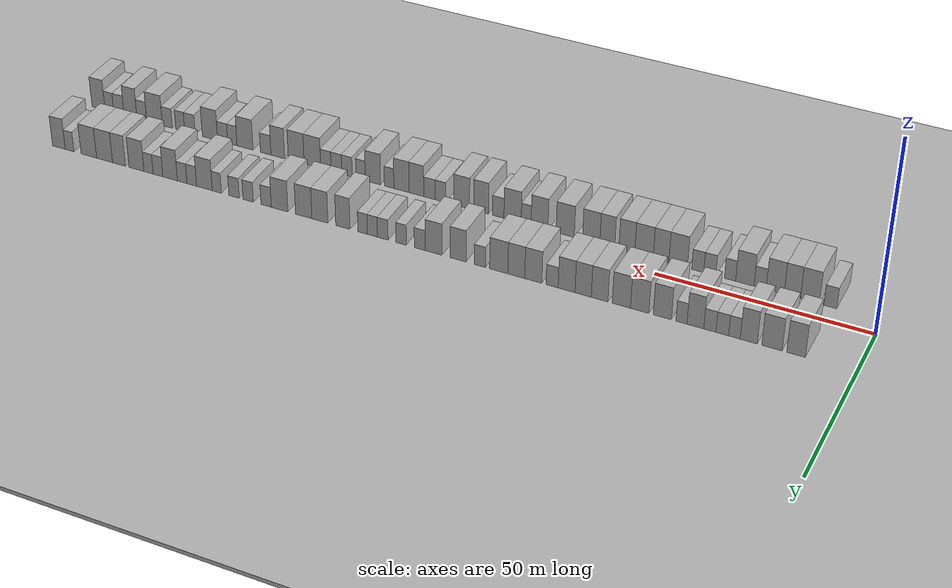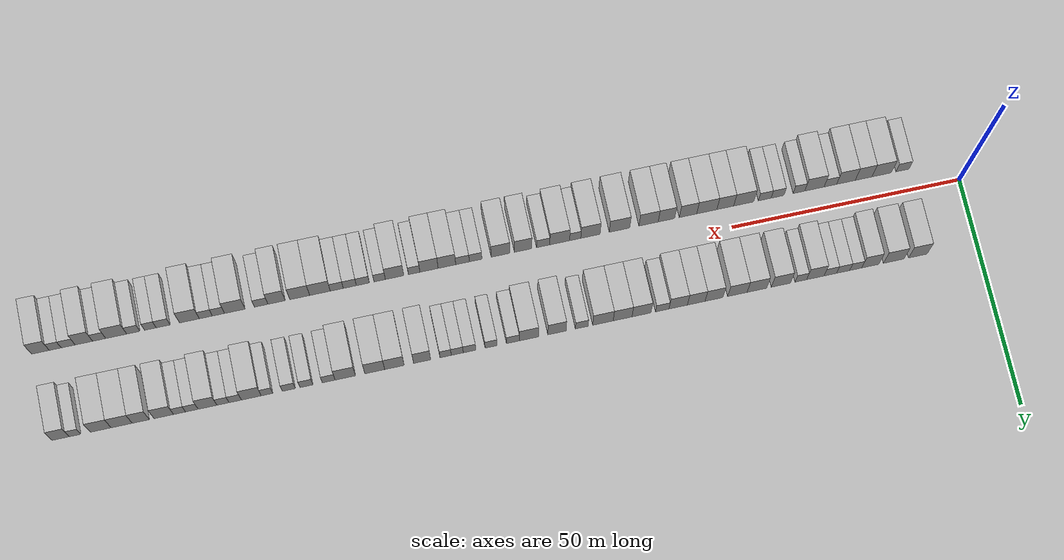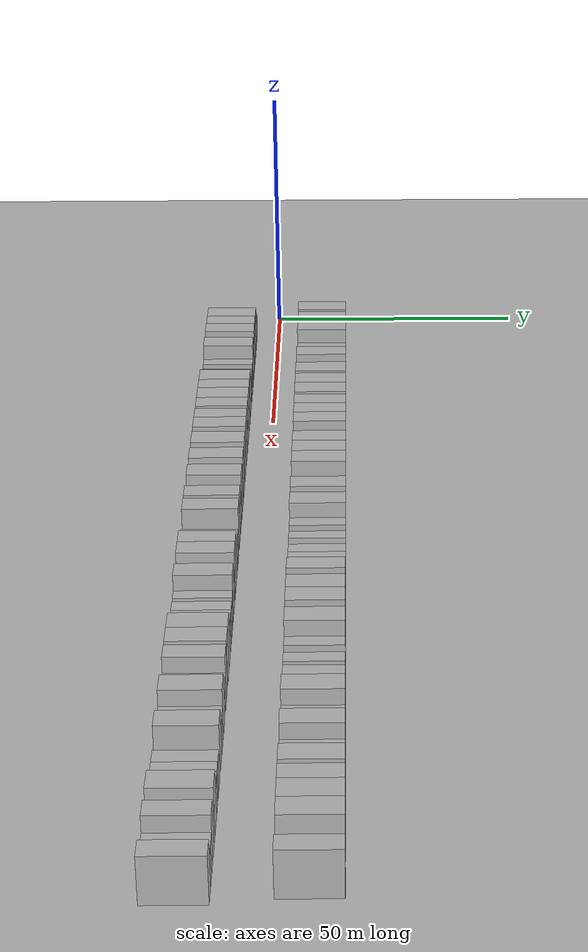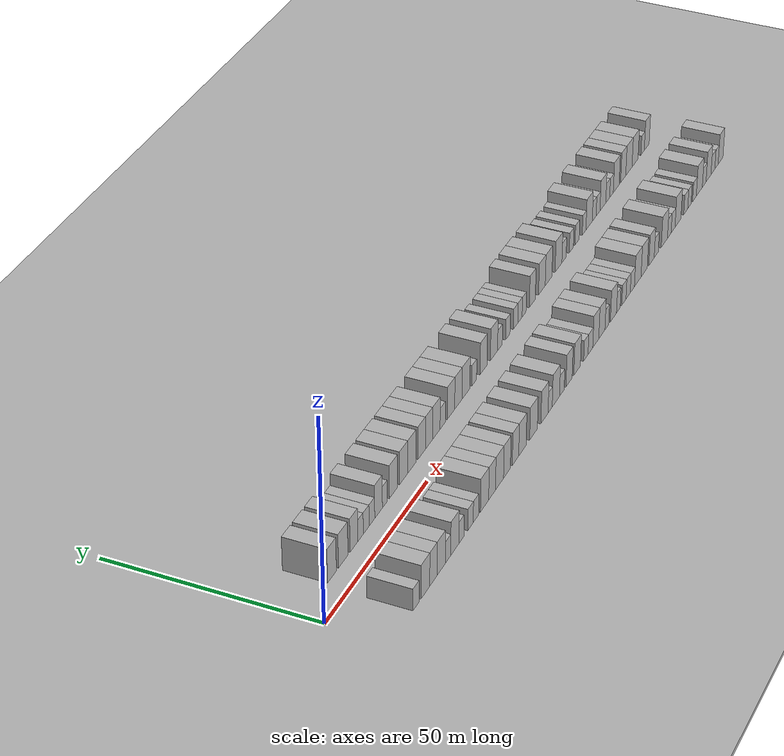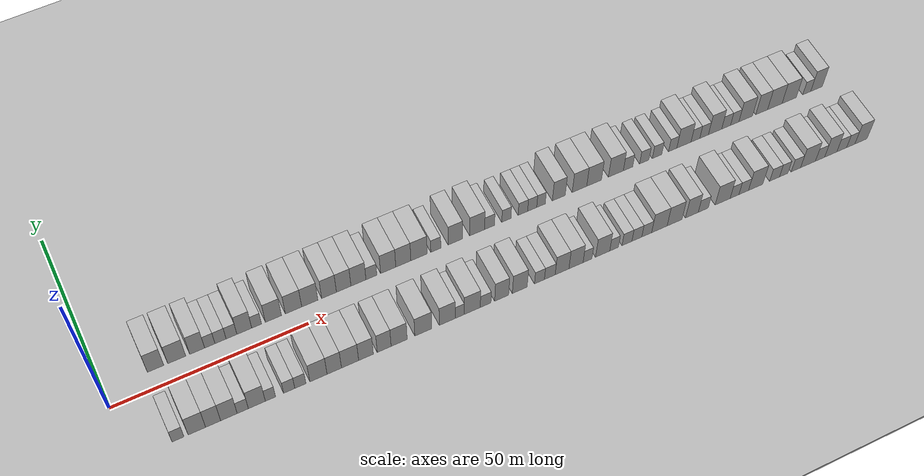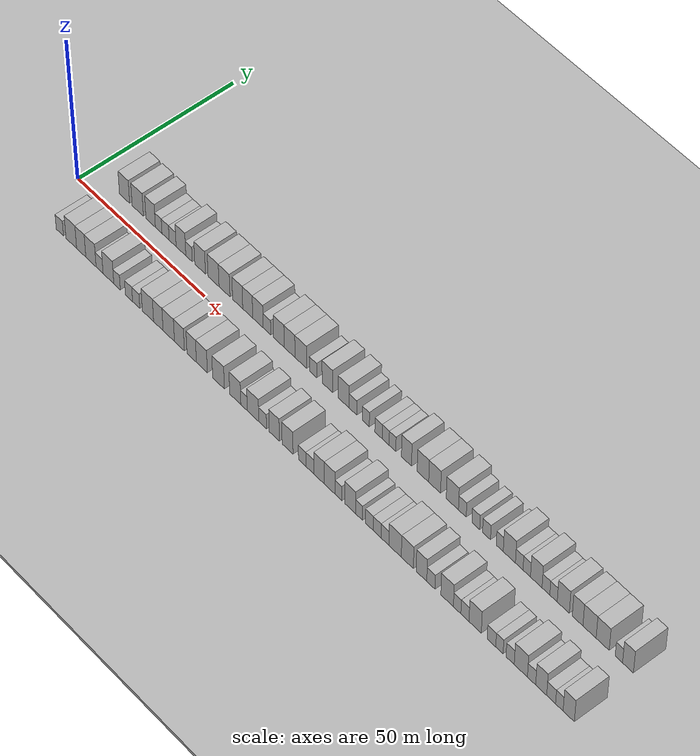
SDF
<?xml version="1.0" encoding="utf-8"?>

<sdf version="1.6">

   <world name="default">

      <gui fullscreen="0">

         <camera name="user_camera">

            <pose>-15 0 4.57585 0 0 0</pose>

            <view_controller>orbit</view_controller>

         </camera>

      </gui>

      <scene>

         <sky>

           <clouds>

             <speed>12</speed>

           </clouds>

         </sky>

         <ambient>0.4 0.4 0.4 1</ambient>

         <background>0.7 0.7 0.7 1</background>

         <shadows>1</shadows>

      </scene>

      <gravity>0 0 -9.8066</gravity>

      <magnetic_field>6e-06 2.3e-05 -4.2e-05</magnetic_field>

      <physics default="0" name="default_physics" type="ode">

         <ode>

            <solver>

               <type>quick</type>

               <iters>10</iters>

               <sor>1.0</sor>

               <use_dynamic_moi_rescaling>0</use_dynamic_moi_rescaling>

            </solver>

            <constraints>

               <cfm>0</cfm>

               <erp>0.2</erp>

               <contact_max_correcting_vel>100</contact_max_correcting_vel>

               <contact_surface_layer>0.001</contact_surface_layer>

            </constraints>

         </ode>

         <max_step_size>0.004</max_step_size>

         <real_time_factor>1</real_time_factor>

         <real_time_update_rate>250</real_time_update_rate>

      </physics>

      <light name="sun" type="directional">

         <cast_shadows>1</cast_shadows>

         <pose>0 0 10 0 0 0</pose>

         <diffuse>0.8 0.8 0.8 1</diffuse>

         <specular>0.2 0.2 0.2 1</specular>

         <attenuation>

            <range>1000</range>

            <constant>0.9</constant>

            <linear>0.01</linear>

            <quadratic>0.001</quadratic>

         </attenuation>

         <direction>-0.5 0.1 -0.9</direction>

      </light>

      <include>

         <name>ground_plane_1</name>

         <uri>model://HANNAS_ground_plane</uri>

         <pose>0 0 0  0 0 0</pose>

      </include>

      <include>

         <name>ground_plane_2</name>

         <uri>model://HANNAS_ground_plane</uri>

         <pose>100 0 0  0 0 0</pose>

      </include>

      <model name="building_1">

         <static>1</static>

         <pose frame="">13.0396 9.5000 0 0.000000 0.000000 1.570796</pose>

         <link name="link">

            <pose frame="">0 0 4.50 0 0 0</pose>

            <collision name="collision">

               <geometry>

                  <box>

                     <size>10.0000 4.0791 9.0000</size>

                  </box>

               </geometry>

               <max_contacts>10</max_contacts>

               <surface>

                  <contact>

                     <ode/>

                  </contact>

                  <bounce/>

                  <friction>

                     <torsional>

                        <ode/>

                     </torsional>

                     <ode/>

                  </friction>

               </surface>

            </collision>

            <visual name="visual">

               <cast_shadows>0</cast_shadows>

               <geometry>

                  <box>

                     <size>10.0000 4.0791 9.0000</size>

                  </box>

               </geometry>

               <material>

                  <script>

                     <uri>model://HANNAS_wall/materials/scripts</uri>

                     <uri>model://HANNAS_wall/materials/textures</uri>

                     <name>vrc/HANNAS_wall</name>

                  </script>

               </material>

            </visual>

            <self_collide>0</self_collide>

            <enable_wind>0</enable_wind>

            <kinematic>0</kinematic>

         </link>

      </model>

      <model name="building_2">

         <static>1</static>

         <pose frame="">18.3261 9.5000 0 0.000000 0.000000 1.570796</pose>

         <link name="link">

            <pose frame="">0 0 4.50 0 0 0</pose>

            <collision name="collision">

               <geometry>

                  <box>

                     <size>10.0000 4.4939 9.0000</size>

                  </box>

               </geometry>

               <max_contacts>10</max_contacts>

               <surface>

                  <contact>

                     <ode/>

                  </contact>

                  <bounce/>

                  <friction>

                     <torsional>

                        <ode/>

                     </torsional>

                     <ode/>

                  </friction>

               </surface>

            </collision>

            <visual name="visual">

               <cast_shadows>0</cast_shadows>

               <geometry>

                  <box>

                     <size>10.0000 4.4939 9.0000</size>

                  </box>

               </geometry>

               <material>

                  <script>

                     <uri>model://HANNAS_wall/materials/scripts</uri>

                     <uri>model://HANNAS_wall/materials/textures</uri>

                     <name>vrc/HANNAS_wall</name>

                  </script>

               </material>

            </visual>

            <self_collide>0</self_collide>

            <enable_wind>0</enable_wind>

            <kinematic>0</kinematic>

         </link>

      </model>

      <model name="building_3">

         <static>1</static>

         <pose frame="">23.4481 9.5000 0 0.000000 0.000000 1.570796</pose>

         <link name="link">

            <pose frame="">0 0 4.50 0 0 0</pose>

            <collision name="collision">

               <geometry>

                  <box>

                     <size>10.0000 3.7502 9.0000</size>

                  </box>

               </geometry>

               <max_contacts>10</max_contacts>

               <surface>

                  <contact>

                     <ode/>

                  </contact>

                  <bounce/>

                  <friction>

                     <torsional>

                        <ode/>

                     </torsional>

                     <ode/>

                  </friction>

               </surface>

            </collision>

            <visual name="visual">

               <cast_shadows>0</cast_shadows>

               <geometry>

                  <box>

                     <size>10.0000 3.7502 9.0000</size>

                  </box>

               </geometry>

               <material>

                  <script>

                     <uri>model://HANNAS_wall/materials/scripts</uri>

                     <uri>model://HANNAS_wall/materials/textures</uri>

                     <name>vrc/HANNAS_wall</name>

                  </script>

               </material>

            </visual>

            <self_collide>0</self_collide>

            <enable_wind>0</enable_wind>

            <kinematic>0</kinematic>

         </link>

      </model>

      <model name="building_4">

         <static>1</static>

         <pose frame="">26.6285 9.5000 0 0.000000 0.000000 1.570796</pose>

         <link name="link">

            <pose frame="">0 0 3.00 0 0 0</pose>

            <collision name="collision">

               <geometry>

                  <box>

                     <size>10.0000 2.6105 6.0000</size>

                  </box>

               </geometry>

               <max_contacts>10</max_contacts>

               <surface>

                  <contact>

                     <ode/>

                  </contact>

                  <bounce/>

                  <friction>

                     <torsional>

                        <ode/>

                     </torsional>

                     <ode/>

                  </friction>

               </surface>

            </collision>

            <visual name="visual">

               <cast_shadows>0</cast_shadows>

               <geometry>

                  <box>

                     <size>10.0000 2.6105 6.0000</size>

                  </box>

               </geometry>

               <material>

                  <script>

                     <uri>model://HANNAS_wall/materials/scripts</uri>

                     <uri>model://HANNAS_wall/materials/textures</uri>

                     <name>vrc/HANNAS_wall</name>

                  </script>

               </material>

            </visual>

            <self_collide>0</self_collide>

            <enable_wind>0</enable_wind>

            <kinematic>0</kinematic>

         </link>

      </model>

      <model name="building_5">

         <static>1</static>

         <pose frame="">29.3491 9.5000 0 0.000000 0.000000 1.570796</pose>

         <link name="link">

            <pose frame="">0 0 3.00 0 0 0</pose>

            <collision name="collision">

               <geometry>

                  <box>

                     <size>10.0000 2.8308 6.0000</size>

                  </box>

               </geometry>

               <max_contacts>10</max_contacts>

               <surface>

                  <contact>

                     <ode/>

                  </contact>

                  <bounce/>

                  <friction>

                     <torsional>

                        <ode/>

                     </torsional>

                     <ode/>

                  </friction>

               </surface>

            </collision>

            <visual name="visual">

               <cast_shadows>0</cast_shadows>

               <geometry>

                  <box>

                     <size>10.0000 2.8308 6.0000</size>

                  </box>

               </geometry>

               <material>

                  <script>

                     <uri>model://HANNAS_wall/materials/scripts</uri>

                     <uri>model://HANNAS_wall/materials/textures</uri>

                     <name>vrc/HANNAS_wall</name>

                  </script>

               </material>

            </visual>

            <self_collide>0</self_collide>

            <enable_wind>0</enable_wind>

            <kinematic>0</kinematic>

         </link>

      </model>

      <model name="building_6">

         <static>1</static>

         <pose frame="">32.1376 9.5000 0 0.000000 0.000000 1.570796</pose>

         <link name="link">

            <pose frame="">0 0 3.00 0 0 0</pose>

            <collision name="collision">

               <geometry>

                  <box>

                     <size>10.0000 2.7462 6.0000</size>

                  </box>

               </geometry>

               <max_contacts>10</max_contacts>

               <surface>

                  <contact>

                     <ode/>

                  </contact>

                  <bounce/>

                  <friction>

                     <torsional>

                        <ode/>

                     </torsional>

                     <ode/>

                  </friction>

               </surface>

            </collision>

            <visual name="visual">

               <cast_shadows>0</cast_shadows>

               <geometry>

                  <box>

                     <size>10.0000 2.7462 6.0000</size>

                  </box>

               </geometry>

               <material>

                  <script>

                     <uri>model://HANNAS_wall/materials/scripts</uri>

                     <uri>model://HANNAS_wall/materials/textures</uri>

                     <name>vrc/HANNAS_wall</name>

                  </script>

               </material>

            </visual>

            <self_collide>0</self_collide>

            <enable_wind>0</enable_wind>

            <kinematic>0</kinematic>

         </link>

      </model>

      <model name="building_7">

         <static>1</static>

         <pose frame="">35.4104 9.5000 0 0.000000 0.000000 1.570796</pose>

         <link name="link">

            <pose frame="">0 0 4.50 0 0 0</pose>

            <collision name="collision">

               <geometry>

                  <box>

                     <size>10.0000 3.7995 9.0000</size>

                  </box>

               </geometry>

               <max_contacts>10</max_contacts>

               <surface>

                  <contact>

                     <ode/>

                  </contact>

                  <bounce/>

                  <friction>

                     <torsional>

                        <ode/>

                     </torsional>

                     <ode/>

                  </friction>

               </surface>

            </collision>

            <visual name="visual">

               <cast_shadows>0</cast_shadows>

               <geometry>

                  <box>

                     <size>10.0000 3.7995 9.0000</size>

                  </box>

               </geometry>

               <material>

                  <script>

                     <uri>model://HANNAS_wall/materials/scripts</uri>

                     <uri>model://HANNAS_wall/materials/textures</uri>

                     <name>vrc/HANNAS_wall</name>

                  </script>

               </material>

            </visual>

            <self_collide>0</self_collide>

            <enable_wind>0</enable_wind>

            <kinematic>0</kinematic>

         </link>

      </model>

      <model name="building_8">

         <static>1</static>

         <pose frame="">38.5644 9.5000 0 0.000000 0.000000 1.570796</pose>

         <link name="link">

            <pose frame="">0 0 3.00 0 0 0</pose>

            <collision name="collision">

               <geometry>

                  <box>

                     <size>10.0000 2.5084 6.0000</size>

                  </box>

               </geometry>

               <max_contacts>10</max_contacts>

               <surface>

                  <contact>

                     <ode/>

                  </contact>

                  <bounce/>

                  <friction>

                     <torsional>

                        <ode/>

                     </torsional>

                     <ode/>

                  </friction>

               </surface>

            </collision>

            <visual name="visual">

               <cast_shadows>0</cast_shadows>

               <geometry>

                  <box>

                     <size>10.0000 2.5084 6.0000</size>

                  </box>

               </geometry>

               <material>

                  <script>

                     <uri>model://HANNAS_wall/materials/scripts</uri>

                     <uri>model://HANNAS_wall/materials/textures</uri>

                     <name>vrc/HANNAS_wall</name>

                  </script>

               </material>

            </visual>

            <self_collide>0</self_collide>

            <enable_wind>0</enable_wind>

            <kinematic>0</kinematic>

         </link>

      </model>

      <model name="building_9">

         <static>1</static>

         <pose frame="">42.8995 9.5000 0 0.000000 0.000000 1.570796</pose>

         <link name="link">

            <pose frame="">0 0 4.50 0 0 0</pose>

            <collision name="collision">

               <geometry>

                  <box>

                     <size>10.0000 4.1618 9.0000</size>

                  </box>

               </geometry>

               <max_contacts>10</max_contacts>

               <surface>

                  <contact>

                     <ode/>

                  </contact>

                  <bounce/>

                  <friction>

                     <torsional>

                        <ode/>

                     </torsional>

                     <ode/>

                  </friction>

               </surface>

            </collision>

            <visual name="visual">

               <cast_shadows>0</cast_shadows>

               <geometry>

                  <box>

                     <size>10.0000 4.1618 9.0000</size>

                  </box>

               </geometry>

               <material>

                  <script>

                     <uri>model://HANNAS_wall/materials/scripts</uri>

                     <uri>model://HANNAS_wall/materials/textures</uri>

                     <name>vrc/HANNAS_wall</name>

                  </script>

               </material>

            </visual>

            <self_collide>0</self_collide>

            <enable_wind>0</enable_wind>

            <kinematic>0</kinematic>

         </link>

      </model>

      <model name="building_10">

         <static>1</static>

         <pose frame="">48.1074 9.5000 0 0.000000 0.000000 1.570796</pose>

         <link name="link">

            <pose frame="">0 0 4.50 0 0 0</pose>

            <collision name="collision">

               <geometry>

                  <box>

                     <size>10.0000 4.2540 9.0000</size>

                  </box>

               </geometry>

               <max_contacts>10</max_contacts>

               <surface>

                  <contact>

                     <ode/>

                  </contact>

                  <bounce/>

                  <friction>

                     <torsional>

                        <ode/>

                     </torsional>

                     <ode/>

                  </friction>

               </surface>

            </collision>

            <visual name="visual">

               <cast_shadows>0</cast_shadows>

               <geometry>

                  <box>

                     <size>10.0000 4.2540 9.0000</size>

                  </box>

               </geometry>

               <material>

                  <script>

                     <uri>model://HANNAS_wall/materials/scripts</uri>

                     <uri>model://HANNAS_wall/materials/textures</uri>

                     <name>vrc/HANNAS_wall</name>

                  </script>

               </material>

            </visual>

            <self_collide>0</self_collide>

            <enable_wind>0</enable_wind>

            <kinematic>0</kinematic>

         </link>

      </model>

      <model name="building_11">

         <static>1</static>

         <pose frame="">52.3440 9.5000 0 0.000000 0.000000 1.570796</pose>

         <link name="link">

            <pose frame="">0 0 4.50 0 0 0</pose>

            <collision name="collision">

               <geometry>

                  <box>

                     <size>10.0000 4.2192 9.0000</size>

                  </box>

               </geometry>

               <max_contacts>10</max_contacts>

               <surface>

                  <contact>

                     <ode/>

                  </contact>

                  <bounce/>

                  <friction>

                     <torsional>

                        <ode/>

                     </torsional>

                     <ode/>

                  </friction>

               </surface>

            </collision>

            <visual name="visual">

               <cast_shadows>0</cast_shadows>

               <geometry>

                  <box>

                     <size>10.0000 4.2192 9.0000</size>

                  </box>

               </geometry>

               <material>

                  <script>

                     <uri>model://HANNAS_wall/materials/scripts</uri>

                     <uri>model://HANNAS_wall/materials/textures</uri>

                     <name>vrc/HANNAS_wall</name>

                  </script>

               </material>

            </visual>

            <self_collide>0</self_collide>

            <enable_wind>0</enable_wind>

            <kinematic>0</kinematic>

         </link>

      </model>

      <model name="building_12">

         <static>1</static>

         <pose frame="">57.3987 9.5000 0 0.000000 0.000000 1.570796</pose>

         <link name="link">

            <pose frame="">0 0 4.50 0 0 0</pose>

            <collision name="collision">

               <geometry>

                  <box>

                     <size>10.0000 3.8903 9.0000</size>

                  </box>

               </geometry>

               <max_contacts>10</max_contacts>

               <surface>

                  <contact>

                     <ode/>

                  </contact>

                  <bounce/>

                  <friction>

                     <torsional>

                        <ode/>

                     </torsional>

                     <ode/>

                  </friction>

               </surface>

            </collision>

            <visual name="visual">

               <cast_shadows>0</cast_shadows>

               <geometry>

                  <box>

                     <size>10.0000 3.8903 9.0000</size>

                  </box>

               </geometry>

               <material>

                  <script>

                     <uri>model://HANNAS_wall/materials/scripts</uri>

                     <uri>model://HANNAS_wall/materials/textures</uri>

                     <name>vrc/HANNAS_wall</name>

                  </script>

               </material>

            </visual>

            <self_collide>0</self_collide>

            <enable_wind>0</enable_wind>

            <kinematic>0</kinematic>

         </link>

      </model>

      <model name="building_13">

         <static>1</static>

         <pose frame="">61.2580 9.5000 0 0.000000 0.000000 1.570796</pose>

         <link name="link">

            <pose frame="">0 0 4.50 0 0 0</pose>

            <collision name="collision">

               <geometry>

                  <box>

                     <size>10.0000 3.8283 9.0000</size>

                  </box>

               </geometry>

               <max_contacts>10</max_contacts>

               <surface>

                  <contact>

                     <ode/>

                  </contact>

                  <bounce/>

                  <friction>

                     <torsional>

                        <ode/>

                     </torsional>

                     <ode/>

                  </friction>

               </surface>

            </collision>

            <visual name="visual">

               <cast_shadows>0</cast_shadows>

               <geometry>

                  <box>

                     <size>10.0000 3.8283 9.0000</size>

                  </box>

               </geometry>

               <material>

                  <script>

                     <uri>model://HANNAS_wall/materials/scripts</uri>

                     <uri>model://HANNAS_wall/materials/textures</uri>

                     <name>vrc/HANNAS_wall</name>

                  </script>

               </material>

            </visual>

            <self_collide>0</self_collide>

            <enable_wind>0</enable_wind>

            <kinematic>0</kinematic>

         </link>

      </model>

      <model name="building_14">

         <static>1</static>

         <pose frame="">65.1616 9.5000 0 0.000000 0.000000 1.570796</pose>

         <link name="link">

            <pose frame="">0 0 4.50 0 0 0</pose>

            <collision name="collision">

               <geometry>

                  <box>

                     <size>10.0000 3.9790 9.0000</size>

                  </box>

               </geometry>

               <max_contacts>10</max_contacts>

               <surface>

                  <contact>

                     <ode/>

                  </contact>

                  <bounce/>

                  <friction>

                     <torsional>

                        <ode/>

                     </torsional>

                     <ode/>

                  </friction>

               </surface>

            </collision>

            <visual name="visual">

               <cast_shadows>0</cast_shadows>

               <geometry>

                  <box>

                     <size>10.0000 3.9790 9.0000</size>

                  </box>

               </geometry>

               <material>

                  <script>

                     <uri>model://HANNAS_wall/materials/scripts</uri>

                     <uri>model://HANNAS_wall/materials/textures</uri>

                     <name>vrc/HANNAS_wall</name>

                  </script>

               </material>

            </visual>

            <self_collide>0</self_collide>

            <enable_wind>0</enable_wind>

            <kinematic>0</kinematic>

         </link>

      </model>

      <model name="building_15">

         <static>1</static>

         <pose frame="">68.5978 9.5000 0 0.000000 0.000000 1.570796</pose>

         <link name="link">

            <pose frame="">0 0 3.00 0 0 0</pose>

            <collision name="collision">

               <geometry>

                  <box>

                     <size>10.0000 2.8933 6.0000</size>

                  </box>

               </geometry>

               <max_contacts>10</max_contacts>

               <surface>

                  <contact>

                     <ode/>

                  </contact>

                  <bounce/>

                  <friction>

                     <torsional>

                        <ode/>

                     </torsional>

                     <ode/>

                  </friction>

               </surface>

            </collision>

            <visual name="visual">

               <cast_shadows>0</cast_shadows>

               <geometry>

                  <box>

                     <size>10.0000 2.8933 6.0000</size>

                  </box>

               </geometry>

               <material>

                  <script>

                     <uri>model://HANNAS_wall/materials/scripts</uri>

                     <uri>model://HANNAS_wall/materials/textures</uri>

                     <name>vrc/HANNAS_wall</name>

                  </script>

               </material>

            </visual>

            <self_collide>0</self_collide>

            <enable_wind>0</enable_wind>

            <kinematic>0</kinematic>

         </link>

      </model>

      <model name="building_16">

         <static>1</static>

         <pose frame="">73.0842 9.5000 0 0.000000 0.000000 1.570796</pose>

         <link name="link">

            <pose frame="">0 0 4.50 0 0 0</pose>

            <collision name="collision">

               <geometry>

                  <box>

                     <size>10.0000 4.0796 9.0000</size>

                  </box>

               </geometry>

               <max_contacts>10</max_contacts>

               <surface>

                  <contact>

                     <ode/>

                  </contact>

                  <bounce/>

                  <friction>

                     <torsional>

                        <ode/>

                     </torsional>

                     <ode/>

                  </friction>

               </surface>

            </collision>

            <visual name="visual">

               <cast_shadows>0</cast_shadows>

               <geometry>

                  <box>

                     <size>10.0000 4.0796 9.0000</size>

                  </box>

               </geometry>

               <material>

                  <script>

                     <uri>model://HANNAS_wall/materials/scripts</uri>

                     <uri>model://HANNAS_wall/materials/textures</uri>

                     <name>vrc/HANNAS_wall</name>

                  </script>

               </material>

            </visual>

            <self_collide>0</self_collide>

            <enable_wind>0</enable_wind>

            <kinematic>0</kinematic>

         </link>

      </model>

      <model name="building_17">

         <static>1</static>

         <pose frame="">77.1564 9.5000 0 0.000000 0.000000 1.570796</pose>

         <link name="link">

            <pose frame="">0 0 4.50 0 0 0</pose>

            <collision name="collision">

               <geometry>

                  <box>

                     <size>10.0000 4.0648 9.0000</size>

                  </box>

               </geometry>

               <max_contacts>10</max_contacts>

               <surface>

                  <contact>

                     <ode/>

                  </contact>

                  <bounce/>

                  <friction>

                     <torsional>

                        <ode/>

                     </torsional>

                     <ode/>

                  </friction>

               </surface>

            </collision>

            <visual name="visual">

               <cast_shadows>0</cast_shadows>

               <geometry>

                  <box>

                     <size>10.0000 4.0648 9.0000</size>

                  </box>

               </geometry>

               <material>

                  <script>

                     <uri>model://HANNAS_wall/materials/scripts</uri>

                     <uri>model://HANNAS_wall/materials/textures</uri>

                     <name>vrc/HANNAS_wall</name>

                  </script>

               </material>

            </visual>

            <self_collide>0</self_collide>

            <enable_wind>0</enable_wind>

            <kinematic>0</kinematic>

         </link>

      </model>

      <model name="building_18">

         <static>1</static>

         <pose frame="">81.3913 9.5000 0 0.000000 0.000000 1.570796</pose>

         <link name="link">

            <pose frame="">0 0 4.50 0 0 0</pose>

            <collision name="collision">

               <geometry>

                  <box>

                     <size>10.0000 4.4050 9.0000</size>

                  </box>

               </geometry>

               <max_contacts>10</max_contacts>

               <surface>

                  <contact>

                     <ode/>

                  </contact>

                  <bounce/>

                  <friction>

                     <torsional>

                        <ode/>

                     </torsional>

                     <ode/>

                  </friction>

               </surface>

            </collision>

            <visual name="visual">

               <cast_shadows>0</cast_shadows>

               <geometry>

                  <box>

                     <size>10.0000 4.4050 9.0000</size>

                  </box>

               </geometry>

               <material>

                  <script>

                     <uri>model://HANNAS_wall/materials/scripts</uri>

                     <uri>model://HANNAS_wall/materials/textures</uri>

                     <name>vrc/HANNAS_wall</name>

                  </script>

               </material>

            </visual>

            <self_collide>0</self_collide>

            <enable_wind>0</enable_wind>

            <kinematic>0</kinematic>

         </link>

      </model>

      <model name="building_19">

         <static>1</static>

         <pose frame="">85.9540 9.5000 0 0.000000 0.000000 1.570796</pose>

         <link name="link">

            <pose frame="">0 0 3.00 0 0 0</pose>

            <collision name="collision">

               <geometry>

                  <box>

                     <size>10.0000 2.7203 6.0000</size>

                  </box>

               </geometry>

               <max_contacts>10</max_contacts>

               <surface>

                  <contact>

                     <ode/>

                  </contact>

                  <bounce/>

                  <friction>

                     <torsional>

                        <ode/>

                     </torsional>

                     <ode/>

                  </friction>

               </surface>

            </collision>

            <visual name="visual">

               <cast_shadows>0</cast_shadows>

               <geometry>

                  <box>

                     <size>10.0000 2.7203 6.0000</size>

                  </box>

               </geometry>

               <material>

                  <script>

                     <uri>model://HANNAS_wall/materials/scripts</uri>

                     <uri>model://HANNAS_wall/materials/textures</uri>

                     <name>vrc/HANNAS_wall</name>

                  </script>

               </material>

            </visual>

            <self_collide>0</self_collide>

            <enable_wind>0</enable_wind>

            <kinematic>0</kinematic>

         </link>

      </model>

      <model name="building_20">

         <static>1</static>

         <pose frame="">91.2753 9.5000 0 0.000000 0.000000 1.570796</pose>

         <link name="link">

            <pose frame="">0 0 4.50 0 0 0</pose>

            <collision name="collision">

               <geometry>

                  <box>

                     <size>10.0000 3.9223 9.0000</size>

                  </box>

               </geometry>

               <max_contacts>10</max_contacts>

               <surface>

                  <contact>

                     <ode/>

                  </contact>

                  <bounce/>

                  <friction>

                     <torsional>

                        <ode/>

                     </torsional>

                     <ode/>

                  </friction>

               </surface>

            </collision>

            <visual name="visual">

               <cast_shadows>0</cast_shadows>

               <geometry>

                  <box>

                     <size>10.0000 3.9223 9.0000</size>

                  </box>

               </geometry>

               <material>

                  <script>

                     <uri>model://HANNAS_wall/materials/scripts</uri>

                     <uri>model://HANNAS_wall/materials/textures</uri>

                     <name>vrc/HANNAS_wall</name>

                  </script>

               </material>

            </visual>

            <self_collide>0</self_collide>

            <enable_wind>0</enable_wind>

            <kinematic>0</kinematic>

         </link>

      </model>

      <model name="building_21">

         <static>1</static>

         <pose frame="">97.2928 9.5000 0 0.000000 0.000000 1.570796</pose>

         <link name="link">

            <pose frame="">0 0 4.50 0 0 0</pose>

            <collision name="collision">

               <geometry>

                  <box>

                     <size>10.0000 4.1127 9.0000</size>

                  </box>

               </geometry>

               <max_contacts>10</max_contacts>

               <surface>

                  <contact>

                     <ode/>

                  </contact>

                  <bounce/>

                  <friction>

                     <torsional>

                        <ode/>

                     </torsional>

                     <ode/>

                  </friction>

               </surface>

            </collision>

            <visual name="visual">

               <cast_shadows>0</cast_shadows>

               <geometry>

                  <box>

                     <size>10.0000 4.1127 9.0000</size>

                  </box>

               </geometry>

               <material>

                  <script>

                     <uri>model://HANNAS_wall/materials/scripts</uri>

                     <uri>model://HANNAS_wall/materials/textures</uri>

                     <name>vrc/HANNAS_wall</name>

                  </script>

               </material>

            </visual>

            <self_collide>0</self_collide>

            <enable_wind>0</enable_wind>

            <kinematic>0</kinematic>

         </link>

      </model>

      <model name="building_22">

         <static>1</static>

         <pose frame="">100.7341 9.5000 0 0.000000 0.000000 1.570796</pose>

         <link name="link">

            <pose frame="">0 0 3.00 0 0 0</pose>

            <collision name="collision">

               <geometry>

                  <box>

                     <size>10.0000 2.7700 6.0000</size>

                  </box>

               </geometry>

               <max_contacts>10</max_contacts>

               <surface>

                  <contact>

                     <ode/>

                  </contact>

                  <bounce/>

                  <friction>

                     <torsional>

                        <ode/>

                     </torsional>

                     <ode/>

                  </friction>

               </surface>

            </collision>

            <visual name="visual">

               <cast_shadows>0</cast_shadows>

               <geometry>

                  <box>

                     <size>10.0000 2.7700 6.0000</size>

                  </box>

               </geometry>

               <material>

                  <script>

                     <uri>model://HANNAS_wall/materials/scripts</uri>

                     <uri>model://HANNAS_wall/materials/textures</uri>

                     <name>vrc/HANNAS_wall</name>

                  </script>

               </material>

            </visual>

            <self_collide>0</self_collide>

            <enable_wind>0</enable_wind>

            <kinematic>0</kinematic>

         </link>

      </model>

      <model name="building_23">

         <static>1</static>

         <pose frame="">105.4062 9.5000 0 0.000000 0.000000 1.570796</pose>

         <link name="link">

            <pose frame="">0 0 3.00 0 0 0</pose>

            <collision name="collision">

               <geometry>

                  <box>

                     <size>10.0000 2.5742 6.0000</size>

                  </box>

               </geometry>

               <max_contacts>10</max_contacts>

               <surface>

                  <contact>

                     <ode/>

                  </contact>

                  <bounce/>

                  <friction>

                     <torsional>

                        <ode/>

                     </torsional>

                     <ode/>

                  </friction>

               </surface>

            </collision>

            <visual name="visual">

               <cast_shadows>0</cast_shadows>

               <geometry>

                  <box>

                     <size>10.0000 2.5742 6.0000</size>

                  </box>

               </geometry>

               <material>

                  <script>

                     <uri>model://HANNAS_wall/materials/scripts</uri>

                     <uri>model://HANNAS_wall/materials/textures</uri>

                     <name>vrc/HANNAS_wall</name>

                  </script>

               </material>

            </visual>

            <self_collide>0</self_collide>

            <enable_wind>0</enable_wind>

            <kinematic>0</kinematic>

         </link>

      </model>

      <model name="building_24">

         <static>1</static>

         <pose frame="">110.0311 9.5000 0 0.000000 0.000000 1.570796</pose>

         <link name="link">

            <pose frame="">0 0 3.00 0 0 0</pose>

            <collision name="collision">

               <geometry>

                  <box>

                     <size>10.0000 2.6754 6.0000</size>

                  </box>

               </geometry>

               <max_contacts>10</max_contacts>

               <surface>

                  <contact>

                     <ode/>

                  </contact>

                  <bounce/>

                  <friction>

                     <torsional>

                        <ode/>

                     </torsional>

                     <ode/>

                  </friction>

               </surface>

            </collision>

            <visual name="visual">

               <cast_shadows>0</cast_shadows>

               <geometry>

                  <box>

                     <size>10.0000 2.6754 6.0000</size>

                  </box>

               </geometry>

               <material>

                  <script>

                     <uri>model://HANNAS_wall/materials/scripts</uri>

                     <uri>model://HANNAS_wall/materials/textures</uri>

                     <name>vrc/HANNAS_wall</name>

                  </script>

               </material>

            </visual>

            <self_collide>0</self_collide>

            <enable_wind>0</enable_wind>

            <kinematic>0</kinematic>

         </link>

      </model>

      <model name="building_25">

         <static>1</static>

         <pose frame="">112.6506 9.5000 0 0.000000 0.000000 1.570796</pose>

         <link name="link">

            <pose frame="">0 0 3.00 0 0 0</pose>

            <collision name="collision">

               <geometry>

                  <box>

                     <size>10.0000 2.5636 6.0000</size>

                  </box>

               </geometry>

               <max_contacts>10</max_contacts>

               <surface>

                  <contact>

                     <ode/>

                  </contact>

                  <bounce/>

                  <friction>

                     <torsional>

                        <ode/>

                     </torsional>

                     <ode/>

                  </friction>

               </surface>

            </collision>

            <visual name="visual">

               <cast_shadows>0</cast_shadows>

               <geometry>

                  <box>

                     <size>10.0000 2.5636 6.0000</size>

                  </box>

               </geometry>

               <material>

                  <script>

                     <uri>model://HANNAS_wall/materials/scripts</uri>

                     <uri>model://HANNAS_wall/materials/textures</uri>

                     <name>vrc/HANNAS_wall</name>

                  </script>

               </material>

            </visual>

            <self_collide>0</self_collide>

            <enable_wind>0</enable_wind>

            <kinematic>0</kinematic>

         </link>

      </model>

      <model name="building_26">

         <static>1</static>

         <pose frame="">115.1369 9.5000 0 0.000000 0.000000 1.570796</pose>

         <link name="link">

            <pose frame="">0 0 3.00 0 0 0</pose>

            <collision name="collision">

               <geometry>

                  <box>

                     <size>10.0000 2.4092 6.0000</size>

                  </box>

               </geometry>

               <max_contacts>10</max_contacts>

               <surface>

                  <contact>

                     <ode/>

                  </contact>

                  <bounce/>

                  <friction>

                     <torsional>

                        <ode/>

                     </torsional>

                     <ode/>

                  </friction>

               </surface>

            </collision>

            <visual name="visual">

               <cast_shadows>0</cast_shadows>

               <geometry>

                  <box>

                     <size>10.0000 2.4092 6.0000</size>

                  </box>

               </geometry>

               <material>

                  <script>

                     <uri>model://HANNAS_wall/materials/scripts</uri>

                     <uri>model://HANNAS_wall/materials/textures</uri>

                     <name>vrc/HANNAS_wall</name>

                  </script>

               </material>

            </visual>

            <self_collide>0</self_collide>

            <enable_wind>0</enable_wind>

            <kinematic>0</kinematic>

         </link>

      </model>

      <model name="building_27">

         <static>1</static>

         <pose frame="">120.1690 9.5000 0 0.000000 0.000000 1.570796</pose>

         <link name="link">

            <pose frame="">0 0 4.50 0 0 0</pose>

            <collision name="collision">

               <geometry>

                  <box>

                     <size>10.0000 3.6550 9.0000</size>

                  </box>

               </geometry>

               <max_contacts>10</max_contacts>

               <surface>

                  <contact>

                     <ode/>

                  </contact>

                  <bounce/>

                  <friction>

                     <torsional>

                        <ode/>

                     </torsional>

                     <ode/>

                  </friction>

               </surface>

            </collision>

            <visual name="visual">

               <cast_shadows>0</cast_shadows>

               <geometry>

                  <box>

                     <size>10.0000 3.6550 9.0000</size>

                  </box>

               </geometry>

               <material>

                  <script>

                     <uri>model://HANNAS_wall/materials/scripts</uri>

                     <uri>model://HANNAS_wall/materials/textures</uri>

                     <name>vrc/HANNAS_wall</name>

                  </script>

               </material>

            </visual>

            <self_collide>0</self_collide>

            <enable_wind>0</enable_wind>

            <kinematic>0</kinematic>

         </link>

      </model>

      <model name="building_28">

         <static>1</static>

         <pose frame="">126.0725 9.5000 0 0.000000 0.000000 1.570796</pose>

         <link name="link">

            <pose frame="">0 0 4.50 0 0 0</pose>

            <collision name="collision">

               <geometry>

                  <box>

                     <size>10.0000 4.1520 9.0000</size>

                  </box>

               </geometry>

               <max_contacts>10</max_contacts>

               <surface>

                  <contact>

                     <ode/>

                  </contact>

                  <bounce/>

                  <friction>

                     <torsional>

                        <ode/>

                     </torsional>

                     <ode/>

                  </friction>

               </surface>

            </collision>

            <visual name="visual">

               <cast_shadows>0</cast_shadows>

               <geometry>

                  <box>

                     <size>10.0000 4.1520 9.0000</size>

                  </box>

               </geometry>

               <material>

                  <script>

                     <uri>model://HANNAS_wall/materials/scripts</uri>

                     <uri>model://HANNAS_wall/materials/textures</uri>

                     <name>vrc/HANNAS_wall</name>

                  </script>

               </material>

            </visual>

            <self_collide>0</self_collide>

            <enable_wind>0</enable_wind>

            <kinematic>0</kinematic>

         </link>

      </model>

      <model name="building_29">

         <static>1</static>

         <pose frame="">130.2625 9.5000 0 0.000000 0.000000 1.570796</pose>

         <link name="link">

            <pose frame="">0 0 4.50 0 0 0</pose>

            <collision name="collision">

               <geometry>

                  <box>

                     <size>10.0000 4.2280 9.0000</size>

                  </box>

               </geometry>

               <max_contacts>10</max_contacts>

               <surface>

                  <contact>

                     <ode/>

                  </contact>

                  <bounce/>

                  <friction>

                     <torsional>

                        <ode/>

                     </torsional>

                     <ode/>

                  </friction>

               </surface>

            </collision>

            <visual name="visual">

               <cast_shadows>0</cast_shadows>

               <geometry>

                  <box>

                     <size>10.0000 4.2280 9.0000</size>

                  </box>

               </geometry>

               <material>

                  <script>

                     <uri>model://HANNAS_wall/materials/scripts</uri>

                     <uri>model://HANNAS_wall/materials/textures</uri>

                     <name>vrc/HANNAS_wall</name>

                  </script>

               </material>

            </visual>

            <self_collide>0</self_collide>

            <enable_wind>0</enable_wind>

            <kinematic>0</kinematic>

         </link>

      </model>

      <model name="building_30">

         <static>1</static>

         <pose frame="">136.5454 9.5000 0 0.000000 0.000000 1.570796</pose>

         <link name="link">

            <pose frame="">0 0 4.50 0 0 0</pose>

            <collision name="collision">

               <geometry>

                  <box>

                     <size>10.0000 4.3378 9.0000</size>

                  </box>

               </geometry>

               <max_contacts>10</max_contacts>

               <surface>

                  <contact>

                     <ode/>

                  </contact>

                  <bounce/>

                  <friction>

                     <torsional>

                        <ode/>

                     </torsional>

                     <ode/>

                  </friction>

               </surface>

            </collision>

            <visual name="visual">

               <cast_shadows>0</cast_shadows>

               <geometry>

                  <box>

                     <size>10.0000 4.3378 9.0000</size>

                  </box>

               </geometry>

               <material>

                  <script>

                     <uri>model://HANNAS_wall/materials/scripts</uri>

                     <uri>model://HANNAS_wall/materials/textures</uri>

                     <name>vrc/HANNAS_wall</name>

                  </script>

               </material>

            </visual>

            <self_collide>0</self_collide>

            <enable_wind>0</enable_wind>

            <kinematic>0</kinematic>

         </link>

      </model>

      <model name="building_31">

         <static>1</static>

         <pose frame="">140.0776 9.5000 0 0.000000 0.000000 1.570796</pose>

         <link name="link">

            <pose frame="">0 0 3.00 0 0 0</pose>

            <collision name="collision">

               <geometry>

                  <box>

                     <size>10.0000 2.7265 6.0000</size>

                  </box>

               </geometry>

               <max_contacts>10</max_contacts>

               <surface>

                  <contact>

                     <ode/>

                  </contact>

                  <bounce/>

                  <friction>

                     <torsional>

                        <ode/>

                     </torsional>

                     <ode/>

                  </friction>

               </surface>

            </collision>

            <visual name="visual">

               <cast_shadows>0</cast_shadows>

               <geometry>

                  <box>

                     <size>10.0000 2.7265 6.0000</size>

                  </box>

               </geometry>

               <material>

                  <script>

                     <uri>model://HANNAS_wall/materials/scripts</uri>

                     <uri>model://HANNAS_wall/materials/textures</uri>

                     <name>vrc/HANNAS_wall</name>

                  </script>

               </material>

            </visual>

            <self_collide>0</self_collide>

            <enable_wind>0</enable_wind>

            <kinematic>0</kinematic>

         </link>

      </model>

      <model name="building_32">

         <static>1</static>

         <pose frame="">144.8093 9.5000 0 0.000000 0.000000 1.570796</pose>

         <link name="link">

            <pose frame="">0 0 3.00 0 0 0</pose>

            <collision name="collision">

               <geometry>

                  <box>

                     <size>10.0000 2.7369 6.0000</size>

                  </box>

               </geometry>

               <max_contacts>10</max_contacts>

               <surface>

                  <contact>

                     <ode/>

                  </contact>

                  <bounce/>

                  <friction>

                     <torsional>

                        <ode/>

                     </torsional>

                     <ode/>

                  </friction>

               </surface>

            </collision>

            <visual name="visual">

               <cast_shadows>0</cast_shadows>

               <geometry>

                  <box>

                     <size>10.0000 2.7369 6.0000</size>

                  </box>

               </geometry>

               <material>

                  <script>

                     <uri>model://HANNAS_wall/materials/scripts</uri>

                     <uri>model://HANNAS_wall/materials/textures</uri>

                     <name>vrc/HANNAS_wall</name>

                  </script>

               </material>

            </visual>

            <self_collide>0</self_collide>

            <enable_wind>0</enable_wind>

            <kinematic>0</kinematic>

         </link>

      </model>

      <model name="building_33">

         <static>1</static>

         <pose frame="">148.5664 9.5000 0 0.000000 0.000000 1.570796</pose>

         <link name="link">

            <pose frame="">0 0 3.00 0 0 0</pose>

            <collision name="collision">

               <geometry>

                  <box>

                     <size>10.0000 2.7774 6.0000</size>

                  </box>

               </geometry>

               <max_contacts>10</max_contacts>

               <surface>

                  <contact>

                     <ode/>

                  </contact>

                  <bounce/>

                  <friction>

                     <torsional>

                        <ode/>

                     </torsional>

                     <ode/>

                  </friction>

               </surface>

            </collision>

            <visual name="visual">

               <cast_shadows>0</cast_shadows>

               <geometry>

                  <box>

                     <size>10.0000 2.7774 6.0000</size>

                  </box>

               </geometry>

               <material>

                  <script>

                     <uri>model://HANNAS_wall/materials/scripts</uri>

                     <uri>model://HANNAS_wall/materials/textures</uri>

                     <name>vrc/HANNAS_wall</name>

                  </script>

               </material>

            </visual>

            <self_collide>0</self_collide>

            <enable_wind>0</enable_wind>

            <kinematic>0</kinematic>

         </link>

      </model>

      <model name="building_34">

         <static>1</static>

         <pose frame="">153.1782 9.5000 0 0.000000 0.000000 1.570796</pose>

         <link name="link">

            <pose frame="">0 0 3.00 0 0 0</pose>

            <collision name="collision">

               <geometry>

                  <box>

                     <size>10.0000 2.4462 6.0000</size>

                  </box>

               </geometry>

               <max_contacts>10</max_contacts>

               <surface>

                  <contact>

                     <ode/>

                  </contact>

                  <bounce/>

                  <friction>

                     <torsional>

                        <ode/>

                     </torsional>

                     <ode/>

                  </friction>

               </surface>

            </collision>

            <visual name="visual">

               <cast_shadows>0</cast_shadows>

               <geometry>

                  <box>

                     <size>10.0000 2.4462 6.0000</size>

                  </box>

               </geometry>

               <material>

                  <script>

                     <uri>model://HANNAS_wall/materials/scripts</uri>

                     <uri>model://HANNAS_wall/materials/textures</uri>

                     <name>vrc/HANNAS_wall</name>

                  </script>

               </material>

            </visual>

            <self_collide>0</self_collide>

            <enable_wind>0</enable_wind>

            <kinematic>0</kinematic>

         </link>

      </model>

      <model name="building_35">

         <static>1</static>

         <pose frame="">156.5116 9.5000 0 0.000000 0.000000 1.570796</pose>

         <link name="link">

            <pose frame="">0 0 4.50 0 0 0</pose>

            <collision name="collision">

               <geometry>

                  <box>

                     <size>10.0000 4.2205 9.0000</size>

                  </box>

               </geometry>

               <max_contacts>10</max_contacts>

               <surface>

                  <contact>

                     <ode/>

                  </contact>

                  <bounce/>

                  <friction>

                     <torsional>

                        <ode/>

                     </torsional>

                     <ode/>

                  </friction>

               </surface>

            </collision>

            <visual name="visual">

               <cast_shadows>0</cast_shadows>

               <geometry>

                  <box>

                     <size>10.0000 4.2205 9.0000</size>

                  </box>

               </geometry>

               <material>

                  <script>

                     <uri>model://HANNAS_wall/materials/scripts</uri>

                     <uri>model://HANNAS_wall/materials/textures</uri>

                     <name>vrc/HANNAS_wall</name>

                  </script>

               </material>

            </visual>

            <self_collide>0</self_collide>

            <enable_wind>0</enable_wind>

            <kinematic>0</kinematic>

         </link>

      </model>

      <model name="building_36">

         <static>1</static>

         <pose frame="">159.9306 9.5000 0 0.000000 0.000000 1.570796</pose>

         <link name="link">

            <pose frame="">0 0 3.00 0 0 0</pose>

            <collision name="collision">

               <geometry>

                  <box>

                     <size>10.0000 2.6175 6.0000</size>

                  </box>

               </geometry>

               <max_contacts>10</max_contacts>

               <surface>

                  <contact>

                     <ode/>

                  </contact>

                  <bounce/>

                  <friction>

                     <torsional>

                        <ode/>

                     </torsional>

                     <ode/>

                  </friction>

               </surface>

            </collision>

            <visual name="visual">

               <cast_shadows>0</cast_shadows>

               <geometry>

                  <box>

                     <size>10.0000 2.6175 6.0000</size>

                  </box>

               </geometry>

               <material>

                  <script>

                     <uri>model://HANNAS_wall/materials/scripts</uri>

                     <uri>model://HANNAS_wall/materials/textures</uri>

                     <name>vrc/HANNAS_wall</name>

                  </script>

               </material>

            </visual>

            <self_collide>0</self_collide>

            <enable_wind>0</enable_wind>

            <kinematic>0</kinematic>

         </link>

      </model>

      <model name="building_37">

         <static>1</static>

         <pose frame="">162.5271 9.5000 0 0.000000 0.000000 1.570796</pose>

         <link name="link">

            <pose frame="">0 0 3.00 0 0 0</pose>

            <collision name="collision">

               <geometry>

                  <box>

                     <size>10.0000 2.5756 6.0000</size>

                  </box>

               </geometry>

               <max_contacts>10</max_contacts>

               <surface>

                  <contact>

                     <ode/>

                  </contact>

                  <bounce/>

                  <friction>

                     <torsional>

                        <ode/>

                     </torsional>

                     <ode/>

                  </friction>

               </surface>

            </collision>

            <visual name="visual">

               <cast_shadows>0</cast_shadows>

               <geometry>

                  <box>

                     <size>10.0000 2.5756 6.0000</size>

                  </box>

               </geometry>

               <material>

                  <script>

                     <uri>model://HANNAS_wall/materials/scripts</uri>

                     <uri>model://HANNAS_wall/materials/textures</uri>

                     <name>vrc/HANNAS_wall</name>

                  </script>

               </material>

            </visual>

            <self_collide>0</self_collide>

            <enable_wind>0</enable_wind>

            <kinematic>0</kinematic>

         </link>

      </model>

      <model name="building_38">

         <static>1</static>

         <pose frame="">165.7989 9.5000 0 0.000000 0.000000 1.570796</pose>

         <link name="link">

            <pose frame="">0 0 4.50 0 0 0</pose>

            <collision name="collision">

               <geometry>

                  <box>

                     <size>10.0000 3.9678 9.0000</size>

                  </box>

               </geometry>

               <max_contacts>10</max_contacts>

               <surface>

                  <contact>

                     <ode/>

                  </contact>

                  <bounce/>

                  <friction>

                     <torsional>

                        <ode/>

                     </torsional>

                     <ode/>

                  </friction>

               </surface>

            </collision>

            <visual name="visual">

               <cast_shadows>0</cast_shadows>

               <geometry>

                  <box>

                     <size>10.0000 3.9678 9.0000</size>

                  </box>

               </geometry>

               <material>

                  <script>

                     <uri>model://HANNAS_wall/materials/scripts</uri>

                     <uri>model://HANNAS_wall/materials/textures</uri>

                     <name>vrc/HANNAS_wall</name>

                  </script>

               </material>

            </visual>

            <self_collide>0</self_collide>

            <enable_wind>0</enable_wind>

            <kinematic>0</kinematic>

         </link>

      </model>

      <model name="building_39">

         <static>1</static>

         <pose frame="">169.1199 9.5000 0 0.000000 0.000000 1.570796</pose>

         <link name="link">

            <pose frame="">0 0 3.00 0 0 0</pose>

            <collision name="collision">

               <geometry>

                  <box>

                     <size>10.0000 2.6742 6.0000</size>

                  </box>

               </geometry>

               <max_contacts>10</max_contacts>

               <surface>

                  <contact>

                     <ode/>

                  </contact>

                  <bounce/>

                  <friction>

                     <torsional>

                        <ode/>

                     </torsional>

                     <ode/>

                  </friction>

               </surface>

            </collision>

            <visual name="visual">

               <cast_shadows>0</cast_shadows>

               <geometry>

                  <box>

                     <size>10.0000 2.6742 6.0000</size>

                  </box>

               </geometry>

               <material>

                  <script>

                     <uri>model://HANNAS_wall/materials/scripts</uri>

                     <uri>model://HANNAS_wall/materials/textures</uri>

                     <name>vrc/HANNAS_wall</name>

                  </script>

               </material>

            </visual>

            <self_collide>0</self_collide>

            <enable_wind>0</enable_wind>

            <kinematic>0</kinematic>

         </link>

      </model>

      <model name="building_40">

         <static>1</static>

         <pose frame="">171.7165 9.5000 0 0.000000 0.000000 1.570796</pose>

         <link name="link">

            <pose frame="">0 0 3.00 0 0 0</pose>

            <collision name="collision">

               <geometry>

                  <box>

                     <size>10.0000 2.5189 6.0000</size>

                  </box>

               </geometry>

               <max_contacts>10</max_contacts>

               <surface>

                  <contact>

                     <ode/>

                  </contact>

                  <bounce/>

                  <friction>

                     <torsional>

                        <ode/>

                     </torsional>

                     <ode/>

                  </friction>

               </surface>

            </collision>

            <visual name="visual">

               <cast_shadows>0</cast_shadows>

               <geometry>

                  <box>

                     <size>10.0000 2.5189 6.0000</size>

                  </box>

               </geometry>

               <material>

                  <script>

                     <uri>model://HANNAS_wall/materials/scripts</uri>

                     <uri>model://HANNAS_wall/materials/textures</uri>

                     <name>vrc/HANNAS_wall</name>

                  </script>

               </material>

            </visual>

            <self_collide>0</self_collide>

            <enable_wind>0</enable_wind>

            <kinematic>0</kinematic>

         </link>

      </model>

      <model name="building_41">

         <static>1</static>

         <pose frame="">175.0330 9.5000 0 0.000000 0.000000 1.570796</pose>

         <link name="link">

            <pose frame="">0 0 4.50 0 0 0</pose>

            <collision name="collision">

               <geometry>

                  <box>

                     <size>10.0000 4.1142 9.0000</size>

                  </box>

               </geometry>

               <max_contacts>10</max_contacts>

               <surface>

                  <contact>

                     <ode/>

                  </contact>

                  <bounce/>

                  <friction>

                     <torsional>

                        <ode/>

                     </torsional>

                     <ode/>

                  </friction>

               </surface>

            </collision>

            <visual name="visual">

               <cast_shadows>0</cast_shadows>

               <geometry>

                  <box>

                     <size>10.0000 4.1142 9.0000</size>

                  </box>

               </geometry>

               <material>

                  <script>

                     <uri>model://HANNAS_wall/materials/scripts</uri>

                     <uri>model://HANNAS_wall/materials/textures</uri>

                     <name>vrc/HANNAS_wall</name>

                  </script>

               </material>

            </visual>

            <self_collide>0</self_collide>

            <enable_wind>0</enable_wind>

            <kinematic>0</kinematic>

         </link>

      </model>

      <model name="building_42">

         <static>1</static>

         <pose frame="">179.8925 9.5000 0 0.000000 0.000000 1.570796</pose>

         <link name="link">

            <pose frame="">0 0 4.50 0 0 0</pose>

            <collision name="collision">

               <geometry>

                  <box>

                     <size>10.0000 3.6046 9.0000</size>

                  </box>

               </geometry>

               <max_contacts>10</max_contacts>

               <surface>

                  <contact>

                     <ode/>

                  </contact>

                  <bounce/>

                  <friction>

                     <torsional>

                        <ode/>

                     </torsional>

                     <ode/>

                  </friction>

               </surface>

            </collision>

            <visual name="visual">

               <cast_shadows>0</cast_shadows>

               <geometry>

                  <box>

                     <size>10.0000 3.6046 9.0000</size>

                  </box>

               </geometry>

               <material>

                  <script>

                     <uri>model://HANNAS_wall/materials/scripts</uri>

                     <uri>model://HANNAS_wall/materials/textures</uri>

                     <name>vrc/HANNAS_wall</name>

                  </script>

               </material>

            </visual>

            <self_collide>0</self_collide>

            <enable_wind>0</enable_wind>

            <kinematic>0</kinematic>

         </link>

      </model>

      <model name="building_43">

         <static>1</static>

         <pose frame="">183.9188 9.5000 0 0.000000 0.000000 1.570796</pose>

         <link name="link">

            <pose frame="">0 0 4.50 0 0 0</pose>

            <collision name="collision">

               <geometry>

                  <box>

                     <size>10.0000 4.4481 9.0000</size>

                  </box>

               </geometry>

               <max_contacts>10</max_contacts>

               <surface>

                  <contact>

                     <ode/>

                  </contact>

                  <bounce/>

                  <friction>

                     <torsional>

                        <ode/>

                     </torsional>

                     <ode/>

                  </friction>

               </surface>

            </collision>

            <visual name="visual">

               <cast_shadows>0</cast_shadows>

               <geometry>

                  <box>

                     <size>10.0000 4.4481 9.0000</size>

                  </box>

               </geometry>

               <material>

                  <script>

                     <uri>model://HANNAS_wall/materials/scripts</uri>

                     <uri>model://HANNAS_wall/materials/textures</uri>

                     <name>vrc/HANNAS_wall</name>

                  </script>

               </material>

            </visual>

            <self_collide>0</self_collide>

            <enable_wind>0</enable_wind>

            <kinematic>0</kinematic>

         </link>

      </model>

      <model name="building_44">

         <static>1</static>

         <pose frame="">188.3335 9.5000 0 0.000000 0.000000 1.570796</pose>

         <link name="link">

            <pose frame="">0 0 4.50 0 0 0</pose>

            <collision name="collision">

               <geometry>

                  <box>

                     <size>10.0000 4.3814 9.0000</size>

                  </box>

               </geometry>

               <max_contacts>10</max_contacts>

               <surface>

                  <contact>

                     <ode/>

                  </contact>

                  <bounce/>

                  <friction>

                     <torsional>

                        <ode/>

                     </torsional>

                     <ode/>

                  </friction>

               </surface>

            </collision>

            <visual name="visual">

               <cast_shadows>0</cast_shadows>

               <geometry>

                  <box>

                     <size>10.0000 4.3814 9.0000</size>

                  </box>

               </geometry>

               <material>

                  <script>

                     <uri>model://HANNAS_wall/materials/scripts</uri>

                     <uri>model://HANNAS_wall/materials/textures</uri>

                     <name>vrc/HANNAS_wall</name>

                  </script>

               </material>

            </visual>

            <self_collide>0</self_collide>

            <enable_wind>0</enable_wind>

            <kinematic>0</kinematic>

         </link>

      </model>

      <model name="building_45">

         <static>1</static>

         <pose frame="">193.7560 9.5000 0 0.000000 0.000000 1.570796</pose>

         <link name="link">

            <pose frame="">0 0 3.00 0 0 0</pose>

            <collision name="collision">

               <geometry>

                  <box>

                     <size>10.0000 2.4636 6.0000</size>

                  </box>

               </geometry>

               <max_contacts>10</max_contacts>

               <surface>

                  <contact>

                     <ode/>

                  </contact>

                  <bounce/>

                  <friction>

                     <torsional>

                        <ode/>

                     </torsional>

                     <ode/>

                  </friction>

               </surface>

            </collision>

            <visual name="visual">

               <cast_shadows>0</cast_shadows>

               <geometry>

                  <box>

                     <size>10.0000 2.4636 6.0000</size>

                  </box>

               </geometry>

               <material>

                  <script>

                     <uri>model://HANNAS_wall/materials/scripts</uri>

                     <uri>model://HANNAS_wall/materials/textures</uri>

                     <name>vrc/HANNAS_wall</name>

                  </script>

               </material>

            </visual>

            <self_collide>0</self_collide>

            <enable_wind>0</enable_wind>

            <kinematic>0</kinematic>

         </link>

      </model>

      <model name="building_46">

         <static>1</static>

         <pose frame="">196.7881 9.5000 0 0.000000 0.000000 1.570796</pose>

         <link name="link">

            <pose frame="">0 0 4.50 0 0 0</pose>

            <collision name="collision">

               <geometry>

                  <box>

                     <size>10.0000 3.6006 9.0000</size>

                  </box>

               </geometry>

               <max_contacts>10</max_contacts>

               <surface>

                  <contact>

                     <ode/>

                  </contact>

                  <bounce/>

                  <friction>

                     <torsional>

                        <ode/>

                     </torsional>

                     <ode/>

                  </friction>

               </surface>

            </collision>

            <visual name="visual">

               <cast_shadows>0</cast_shadows>

               <geometry>

                  <box>

                     <size>10.0000 3.6006 9.0000</size>

                  </box>

               </geometry>

               <material>

                  <script>

                     <uri>model://HANNAS_wall/materials/scripts</uri>

                     <uri>model://HANNAS_wall/materials/textures</uri>

                     <name>vrc/HANNAS_wall</name>

                  </script>

               </material>

            </visual>

            <self_collide>0</self_collide>

            <enable_wind>0</enable_wind>

            <kinematic>0</kinematic>

         </link>

      </model>

      <model name="building_47">

         <static>1</static>

         <pose frame="">11.4581 -9.5000 0 0.000000 0.000000 1.570796</pose>

         <link name="link">

            <pose frame="">0 0 3.00 0 0 0</pose>

            <collision name="collision">

               <geometry>

                  <box>

                     <size>10.0000 2.9162 6.0000</size>

                  </box>

               </geometry>

               <max_contacts>10</max_contacts>

               <surface>

                  <contact>

                     <ode/>

                  </contact>

                  <bounce/>

                  <friction>

                     <torsional>

                        <ode/>

                     </torsional>

                     <ode/>

                  </friction>

               </surface>

            </collision>

            <visual name="visual">

               <cast_shadows>0</cast_shadows>

               <geometry>

                  <box>

                     <size>10.0000 2.9162 6.0000</size>

                  </box>

               </geometry>

               <material>

                  <script>

                     <uri>model://HANNAS_wall/materials/scripts</uri>

                     <uri>model://HANNAS_wall/materials/textures</uri>

                     <name>vrc/HANNAS_wall</name>

                  </script>

               </material>

            </visual>

            <self_collide>0</self_collide>

            <enable_wind>0</enable_wind>

            <kinematic>0</kinematic>

         </link>

      </model>

      <model name="building_48">

         <static>1</static>

         <pose frame="">16.0520 -9.5000 0 0.000000 0.000000 1.570796</pose>

         <link name="link">

            <pose frame="">0 0 4.50 0 0 0</pose>

            <collision name="collision">

               <geometry>

                  <box>

                     <size>10.0000 4.2716 9.0000</size>

                  </box>

               </geometry>

               <max_contacts>10</max_contacts>

               <surface>

                  <contact>

                     <ode/>

                  </contact>

                  <bounce/>

                  <friction>

                     <torsional>

                        <ode/>

                     </torsional>

                     <ode/>

                  </friction>

               </surface>

            </collision>

            <visual name="visual">

               <cast_shadows>0</cast_shadows>

               <geometry>

                  <box>

                     <size>10.0000 4.2716 9.0000</size>

                  </box>

               </geometry>

               <material>

                  <script>

                     <uri>model://HANNAS_wall/materials/scripts</uri>

                     <uri>model://HANNAS_wall/materials/textures</uri>

                     <name>vrc/HANNAS_wall</name>

                  </script>

               </material>

            </visual>

            <self_collide>0</self_collide>

            <enable_wind>0</enable_wind>

            <kinematic>0</kinematic>

         </link>

      </model>

      <model name="building_49">

         <static>1</static>

         <pose frame="">20.0341 -9.5000 0 0.000000 0.000000 1.570796</pose>

         <link name="link">

            <pose frame="">0 0 4.50 0 0 0</pose>

            <collision name="collision">

               <geometry>

                  <box>

                     <size>10.0000 3.6925 9.0000</size>

                  </box>

               </geometry>

               <max_contacts>10</max_contacts>

               <surface>

                  <contact>

                     <ode/>

                  </contact>

                  <bounce/>

                  <friction>

                     <torsional>

                        <ode/>

                     </torsional>

                     <ode/>

                  </friction>

               </surface>

            </collision>

            <visual name="visual">

               <cast_shadows>0</cast_shadows>

               <geometry>

                  <box>

                     <size>10.0000 3.6925 9.0000</size>

                  </box>

               </geometry>

               <material>

                  <script>

                     <uri>model://HANNAS_wall/materials/scripts</uri>

                     <uri>model://HANNAS_wall/materials/textures</uri>

                     <name>vrc/HANNAS_wall</name>

                  </script>

               </material>

            </visual>

            <self_collide>0</self_collide>

            <enable_wind>0</enable_wind>

            <kinematic>0</kinematic>

         </link>

      </model>

      <model name="building_50">

         <static>1</static>

         <pose frame="">23.9258 -9.5000 0 0.000000 0.000000 1.570796</pose>

         <link name="link">

            <pose frame="">0 0 4.50 0 0 0</pose>

            <collision name="collision">

               <geometry>

                  <box>

                     <size>10.0000 4.0909 9.0000</size>

                  </box>

               </geometry>

               <max_contacts>10</max_contacts>

               <surface>

                  <contact>

                     <ode/>

                  </contact>

                  <bounce/>

                  <friction>

                     <torsional>

                        <ode/>

                     </torsional>

                     <ode/>

                  </friction>

               </surface>

            </collision>

            <visual name="visual">

               <cast_shadows>0</cast_shadows>

               <geometry>

                  <box>

                     <size>10.0000 4.0909 9.0000</size>

                  </box>

               </geometry>

               <material>

                  <script>

                     <uri>model://HANNAS_wall/materials/scripts</uri>

                     <uri>model://HANNAS_wall/materials/textures</uri>

                     <name>vrc/HANNAS_wall</name>

                  </script>

               </material>

            </visual>

            <self_collide>0</self_collide>

            <enable_wind>0</enable_wind>

            <kinematic>0</kinematic>

         </link>

      </model>

      <model name="building_51">

         <static>1</static>

         <pose frame="">27.3574 -9.5000 0 0.000000 0.000000 1.570796</pose>

         <link name="link">

            <pose frame="">0 0 3.00 0 0 0</pose>

            <collision name="collision">

               <geometry>

                  <box>

                     <size>10.0000 2.7722 6.0000</size>

                  </box>

               </geometry>

               <max_contacts>10</max_contacts>

               <surface>

                  <contact>

                     <ode/>

                  </contact>

                  <bounce/>

                  <friction>

                     <torsional>

                        <ode/>

                     </torsional>

                     <ode/>

                  </friction>

               </surface>

            </collision>

            <visual name="visual">

               <cast_shadows>0</cast_shadows>

               <geometry>

                  <box>

                     <size>10.0000 2.7722 6.0000</size>

                  </box>

               </geometry>

               <material>

                  <script>

                     <uri>model://HANNAS_wall/materials/scripts</uri>

                     <uri>model://HANNAS_wall/materials/textures</uri>

                     <name>vrc/HANNAS_wall</name>

                  </script>

               </material>

            </visual>

            <self_collide>0</self_collide>

            <enable_wind>0</enable_wind>

            <kinematic>0</kinematic>

         </link>

      </model>

      <model name="building_52">

         <static>1</static>

         <pose frame="">30.8595 -9.5000 0 0.000000 0.000000 1.570796</pose>

         <link name="link">

            <pose frame="">0 0 4.50 0 0 0</pose>

            <collision name="collision">

               <geometry>

                  <box>

                     <size>10.0000 4.2320 9.0000</size>

                  </box>

               </geometry>

               <max_contacts>10</max_contacts>

               <surface>

                  <contact>

                     <ode/>

                  </contact>

                  <bounce/>

                  <friction>

                     <torsional>

                        <ode/>

                     </torsional>

                     <ode/>

                  </friction>

               </surface>

            </collision>

            <visual name="visual">

               <cast_shadows>0</cast_shadows>

               <geometry>

                  <box>

                     <size>10.0000 4.2320 9.0000</size>

                  </box>

               </geometry>

               <material>

                  <script>

                     <uri>model://HANNAS_wall/materials/scripts</uri>

                     <uri>model://HANNAS_wall/materials/textures</uri>

                     <name>vrc/HANNAS_wall</name>

                  </script>

               </material>

            </visual>

            <self_collide>0</self_collide>

            <enable_wind>0</enable_wind>

            <kinematic>0</kinematic>

         </link>

      </model>

      <model name="building_53">

         <static>1</static>

         <pose frame="">34.2607 -9.5000 0 0.000000 0.000000 1.570796</pose>

         <link name="link">

            <pose frame="">0 0 3.00 0 0 0</pose>

            <collision name="collision">

               <geometry>

                  <box>

                     <size>10.0000 2.5706 6.0000</size>

                  </box>

               </geometry>

               <max_contacts>10</max_contacts>

               <surface>

                  <contact>

                     <ode/>

                  </contact>

                  <bounce/>

                  <friction>

                     <torsional>

                        <ode/>

                     </torsional>

                     <ode/>

                  </friction>

               </surface>

            </collision>

            <visual name="visual">

               <cast_shadows>0</cast_shadows>

               <geometry>

                  <box>

                     <size>10.0000 2.5706 6.0000</size>

                  </box>

               </geometry>

               <material>

                  <script>

                     <uri>model://HANNAS_wall/materials/scripts</uri>

                     <uri>model://HANNAS_wall/materials/textures</uri>

                     <name>vrc/HANNAS_wall</name>

                  </script>

               </material>

            </visual>

            <self_collide>0</self_collide>

            <enable_wind>0</enable_wind>

            <kinematic>0</kinematic>

         </link>

      </model>

      <model name="building_54">

         <static>1</static>

         <pose frame="">38.9569 -9.5000 0 0.000000 0.000000 1.570796</pose>

         <link name="link">

            <pose frame="">0 0 3.00 0 0 0</pose>

            <collision name="collision">

               <geometry>

                  <box>

                     <size>10.0000 2.8217 6.0000</size>

                  </box>

               </geometry>

               <max_contacts>10</max_contacts>

               <surface>

                  <contact>

                     <ode/>

                  </contact>

                  <bounce/>

                  <friction>

                     <torsional>

                        <ode/>

                     </torsional>

                     <ode/>

                  </friction>

               </surface>

            </collision>

            <visual name="visual">

               <cast_shadows>0</cast_shadows>

               <geometry>

                  <box>

                     <size>10.0000 2.8217 6.0000</size>

                  </box>

               </geometry>

               <material>

                  <script>

                     <uri>model://HANNAS_wall/materials/scripts</uri>

                     <uri>model://HANNAS_wall/materials/textures</uri>

                     <name>vrc/HANNAS_wall</name>

                  </script>

               </material>

            </visual>

            <self_collide>0</self_collide>

            <enable_wind>0</enable_wind>

            <kinematic>0</kinematic>

         </link>

      </model>

      <model name="building_55">

         <static>1</static>

         <pose frame="">41.7753 -9.5000 0 0.000000 0.000000 1.570796</pose>

         <link name="link">

            <pose frame="">0 0 3.00 0 0 0</pose>

            <collision name="collision">

               <geometry>

                  <box>

                     <size>10.0000 2.8153 6.0000</size>

                  </box>

               </geometry>

               <max_contacts>10</max_contacts>

               <surface>

                  <contact>

                     <ode/>

                  </contact>

                  <bounce/>

                  <friction>

                     <torsional>

                        <ode/>

                     </torsional>

                     <ode/>

                  </friction>

               </surface>

            </collision>

            <visual name="visual">

               <cast_shadows>0</cast_shadows>

               <geometry>

                  <box>

                     <size>10.0000 2.8153 6.0000</size>

                  </box>

               </geometry>

               <material>

                  <script>

                     <uri>model://HANNAS_wall/materials/scripts</uri>

                     <uri>model://HANNAS_wall/materials/textures</uri>

                     <name>vrc/HANNAS_wall</name>

                  </script>

               </material>

            </visual>

            <self_collide>0</self_collide>

            <enable_wind>0</enable_wind>

            <kinematic>0</kinematic>

         </link>

      </model>

      <model name="building_56">

         <static>1</static>

         <pose frame="">46.3729 -9.5000 0 0.000000 0.000000 1.570796</pose>

         <link name="link">

            <pose frame="">0 0 4.50 0 0 0</pose>

            <collision name="collision">

               <geometry>

                  <box>

                     <size>10.0000 4.3799 9.0000</size>

                  </box>

               </geometry>

               <max_contacts>10</max_contacts>

               <surface>

                  <contact>

                     <ode/>

                  </contact>

                  <bounce/>

                  <friction>

                     <torsional>

                        <ode/>

                     </torsional>

                     <ode/>

                  </friction>

               </surface>

            </collision>

            <visual name="visual">

               <cast_shadows>0</cast_shadows>

               <geometry>

                  <box>

                     <size>10.0000 4.3799 9.0000</size>

                  </box>

               </geometry>

               <material>

                  <script>

                     <uri>model://HANNAS_wall/materials/scripts</uri>

                     <uri>model://HANNAS_wall/materials/textures</uri>

                     <name>vrc/HANNAS_wall</name>

                  </script>

               </material>

            </visual>

            <self_collide>0</self_collide>

            <enable_wind>0</enable_wind>

            <kinematic>0</kinematic>

         </link>

      </model>

      <model name="building_57">

         <static>1</static>

         <pose frame="">50.4060 -9.5000 0 0.000000 0.000000 1.570796</pose>

         <link name="link">

            <pose frame="">0 0 4.50 0 0 0</pose>

            <collision name="collision">

               <geometry>

                  <box>

                     <size>10.0000 3.6864 9.0000</size>

                  </box>

               </geometry>

               <max_contacts>10</max_contacts>

               <surface>

                  <contact>

                     <ode/>

                  </contact>

                  <bounce/>

                  <friction>

                     <torsional>

                        <ode/>

                     </torsional>

                     <ode/>

                  </friction>

               </surface>

            </collision>

            <visual name="visual">

               <cast_shadows>0</cast_shadows>

               <geometry>

                  <box>

                     <size>10.0000 3.6864 9.0000</size>

                  </box>

               </geometry>

               <material>

                  <script>

                     <uri>model://HANNAS_wall/materials/scripts</uri>

                     <uri>model://HANNAS_wall/materials/textures</uri>

                     <name>vrc/HANNAS_wall</name>

                  </script>

               </material>

            </visual>

            <self_collide>0</self_collide>

            <enable_wind>0</enable_wind>

            <kinematic>0</kinematic>

         </link>

      </model>

      <model name="building_58">

         <static>1</static>

         <pose frame="">54.4502 -9.5000 0 0.000000 0.000000 1.570796</pose>

         <link name="link">

            <pose frame="">0 0 4.50 0 0 0</pose>

            <collision name="collision">

               <geometry>

                  <box>

                     <size>10.0000 4.4020 9.0000</size>

                  </box>

               </geometry>

               <max_contacts>10</max_contacts>

               <surface>

                  <contact>

                     <ode/>

                  </contact>

                  <bounce/>

                  <friction>

                     <torsional>

                        <ode/>

                     </torsional>

                     <ode/>

                  </friction>

               </surface>

            </collision>

            <visual name="visual">

               <cast_shadows>0</cast_shadows>

               <geometry>

                  <box>

                     <size>10.0000 4.4020 9.0000</size>

                  </box>

               </geometry>

               <material>

                  <script>

                     <uri>model://HANNAS_wall/materials/scripts</uri>

                     <uri>model://HANNAS_wall/materials/textures</uri>

                     <name>vrc/HANNAS_wall</name>

                  </script>

               </material>

            </visual>

            <self_collide>0</self_collide>

            <enable_wind>0</enable_wind>

            <kinematic>0</kinematic>

         </link>

      </model>

      <model name="building_59">

         <static>1</static>

         <pose frame="">58.5550 -9.5000 0 0.000000 0.000000 1.570796</pose>

         <link name="link">

            <pose frame="">0 0 4.50 0 0 0</pose>

            <collision name="collision">

               <geometry>

                  <box>

                     <size>10.0000 3.8074 9.0000</size>

                  </box>

               </geometry>

               <max_contacts>10</max_contacts>

               <surface>

                  <contact>

                     <ode/>

                  </contact>

                  <bounce/>

                  <friction>

                     <torsional>

                        <ode/>

                     </torsional>

                     <ode/>

                  </friction>

               </surface>

            </collision>

            <visual name="visual">

               <cast_shadows>0</cast_shadows>

               <geometry>

                  <box>

                     <size>10.0000 3.8074 9.0000</size>

                  </box>

               </geometry>

               <material>

                  <script>

                     <uri>model://HANNAS_wall/materials/scripts</uri>

                     <uri>model://HANNAS_wall/materials/textures</uri>

                     <name>vrc/HANNAS_wall</name>

                  </script>

               </material>

            </visual>

            <self_collide>0</self_collide>

            <enable_wind>0</enable_wind>

            <kinematic>0</kinematic>

         </link>

      </model>

      <model name="building_60">

         <static>1</static>

         <pose frame="">63.2596 -9.5000 0 0.000000 0.000000 1.570796</pose>

         <link name="link">

            <pose frame="">0 0 4.50 0 0 0</pose>

            <collision name="collision">

               <geometry>

                  <box>

                     <size>10.0000 3.6018 9.0000</size>

                  </box>

               </geometry>

               <max_contacts>10</max_contacts>

               <surface>

                  <contact>

                     <ode/>

                  </contact>

                  <bounce/>

                  <friction>

                     <torsional>

                        <ode/>

                     </torsional>

                     <ode/>

                  </friction>

               </surface>

            </collision>

            <visual name="visual">

               <cast_shadows>0</cast_shadows>

               <geometry>

                  <box>

                     <size>10.0000 3.6018 9.0000</size>

                  </box>

               </geometry>

               <material>

                  <script>

                     <uri>model://HANNAS_wall/materials/scripts</uri>

                     <uri>model://HANNAS_wall/materials/textures</uri>

                     <name>vrc/HANNAS_wall</name>

                  </script>

               </material>

            </visual>

            <self_collide>0</self_collide>

            <enable_wind>0</enable_wind>

            <kinematic>0</kinematic>

         </link>

      </model>

      <model name="building_61">

         <static>1</static>

         <pose frame="">67.1577 -9.5000 0 0.000000 0.000000 1.570796</pose>

         <link name="link">

            <pose frame="">0 0 4.50 0 0 0</pose>

            <collision name="collision">

               <geometry>

                  <box>

                     <size>10.0000 4.1945 9.0000</size>

                  </box>

               </geometry>

               <max_contacts>10</max_contacts>

               <surface>

                  <contact>

                     <ode/>

                  </contact>

                  <bounce/>

                  <friction>

                     <torsional>

                        <ode/>

                     </torsional>

                     <ode/>

                  </friction>

               </surface>

            </collision>

            <visual name="visual">

               <cast_shadows>0</cast_shadows>

               <geometry>

                  <box>

                     <size>10.0000 4.1945 9.0000</size>

                  </box>

               </geometry>

               <material>

                  <script>

                     <uri>model://HANNAS_wall/materials/scripts</uri>

                     <uri>model://HANNAS_wall/materials/textures</uri>

                     <name>vrc/HANNAS_wall</name>

                  </script>

               </material>

            </visual>

            <self_collide>0</self_collide>

            <enable_wind>0</enable_wind>

            <kinematic>0</kinematic>

         </link>

      </model>

      <model name="building_62">

         <static>1</static>

         <pose frame="">73.4821 -9.5000 0 0.000000 0.000000 1.570796</pose>

         <link name="link">

            <pose frame="">0 0 4.50 0 0 0</pose>

            <collision name="collision">

               <geometry>

                  <box>

                     <size>10.0000 4.4543 9.0000</size>

                  </box>

               </geometry>

               <max_contacts>10</max_contacts>

               <surface>

                  <contact>

                     <ode/>

                  </contact>

                  <bounce/>

                  <friction>

                     <torsional>

                        <ode/>

                     </torsional>

                     <ode/>

                  </friction>

               </surface>

            </collision>

            <visual name="visual">

               <cast_shadows>0</cast_shadows>

               <geometry>

                  <box>

                     <size>10.0000 4.4543 9.0000</size>

                  </box>

               </geometry>

               <material>

                  <script>

                     <uri>model://HANNAS_wall/materials/scripts</uri>

                     <uri>model://HANNAS_wall/materials/textures</uri>

                     <name>vrc/HANNAS_wall</name>

                  </script>

               </material>

            </visual>

            <self_collide>0</self_collide>

            <enable_wind>0</enable_wind>

            <kinematic>0</kinematic>

         </link>

      </model>

      <model name="building_63">

         <static>1</static>

         <pose frame="">79.8026 -9.5000 0 0.000000 0.000000 1.570796</pose>

         <link name="link">

            <pose frame="">0 0 4.50 0 0 0</pose>

            <collision name="collision">

               <geometry>

                  <box>

                     <size>10.0000 4.1866 9.0000</size>

                  </box>

               </geometry>

               <max_contacts>10</max_contacts>

               <surface>

                  <contact>

                     <ode/>

                  </contact>

                  <bounce/>

                  <friction>

                     <torsional>

                        <ode/>

                     </torsional>

                     <ode/>

                  </friction>

               </surface>

            </collision>

            <visual name="visual">

               <cast_shadows>0</cast_shadows>

               <geometry>

                  <box>

                     <size>10.0000 4.1866 9.0000</size>

                  </box>

               </geometry>

               <material>

                  <script>

                     <uri>model://HANNAS_wall/materials/scripts</uri>

                     <uri>model://HANNAS_wall/materials/textures</uri>

                     <name>vrc/HANNAS_wall</name>

                  </script>

               </material>

            </visual>

            <self_collide>0</self_collide>

            <enable_wind>0</enable_wind>

            <kinematic>0</kinematic>

         </link>

      </model>

      <model name="building_64">

         <static>1</static>

         <pose frame="">83.1112 -9.5000 0 0.000000 0.000000 1.570796</pose>

         <link name="link">

            <pose frame="">0 0 3.00 0 0 0</pose>

            <collision name="collision">

               <geometry>

                  <box>

                     <size>10.0000 2.4305 6.0000</size>

                  </box>

               </geometry>

               <max_contacts>10</max_contacts>

               <surface>

                  <contact>

                     <ode/>

                  </contact>

                  <bounce/>

                  <friction>

                     <torsional>

                        <ode/>

                     </torsional>

                     <ode/>

                  </friction>

               </surface>

            </collision>

            <visual name="visual">

               <cast_shadows>0</cast_shadows>

               <geometry>

                  <box>

                     <size>10.0000 2.4305 6.0000</size>

                  </box>

               </geometry>

               <material>

                  <script>

                     <uri>model://HANNAS_wall/materials/scripts</uri>

                     <uri>model://HANNAS_wall/materials/textures</uri>

                     <name>vrc/HANNAS_wall</name>

                  </script>

               </material>

            </visual>

            <self_collide>0</self_collide>

            <enable_wind>0</enable_wind>

            <kinematic>0</kinematic>

         </link>

      </model>

      <model name="building_65">

         <static>1</static>

         <pose frame="">86.4798 -9.5000 0 0.000000 0.000000 1.570796</pose>

         <link name="link">

            <pose frame="">0 0 4.50 0 0 0</pose>

            <collision name="collision">

               <geometry>

                  <box>

                     <size>10.0000 4.3069 9.0000</size>

                  </box>

               </geometry>

               <max_contacts>10</max_contacts>

               <surface>

                  <contact>

                     <ode/>

                  </contact>

                  <bounce/>

                  <friction>

                     <torsional>

                        <ode/>

                     </torsional>

                     <ode/>

                  </friction>

               </surface>

            </collision>

            <visual name="visual">

               <cast_shadows>0</cast_shadows>

               <geometry>

                  <box>

                     <size>10.0000 4.3069 9.0000</size>

                  </box>

               </geometry>

               <material>

                  <script>

                     <uri>model://HANNAS_wall/materials/scripts</uri>

                     <uri>model://HANNAS_wall/materials/textures</uri>

                     <name>vrc/HANNAS_wall</name>

                  </script>

               </material>

            </visual>

            <self_collide>0</self_collide>

            <enable_wind>0</enable_wind>

            <kinematic>0</kinematic>

         </link>

      </model>

      <model name="building_66">

         <static>1</static>

         <pose frame="">90.0707 -9.5000 0 0.000000 0.000000 1.570796</pose>

         <link name="link">

            <pose frame="">0 0 3.00 0 0 0</pose>

            <collision name="collision">

               <geometry>

                  <box>

                     <size>10.0000 2.8748 6.0000</size>

                  </box>

               </geometry>

               <max_contacts>10</max_contacts>

               <surface>

                  <contact>

                     <ode/>

                  </contact>

                  <bounce/>

                  <friction>

                     <torsional>

                        <ode/>

                     </torsional>

                     <ode/>

                  </friction>

               </surface>

            </collision>

            <visual name="visual">

               <cast_shadows>0</cast_shadows>

               <geometry>

                  <box>

                     <size>10.0000 2.8748 6.0000</size>

                  </box>

               </geometry>

               <material>

                  <script>

                     <uri>model://HANNAS_wall/materials/scripts</uri>

                     <uri>model://HANNAS_wall/materials/textures</uri>

                     <name>vrc/HANNAS_wall</name>

                  </script>

               </material>

            </visual>

            <self_collide>0</self_collide>

            <enable_wind>0</enable_wind>

            <kinematic>0</kinematic>

         </link>

      </model>

      <model name="building_67">

         <static>1</static>

         <pose frame="">94.3955 -9.5000 0 0.000000 0.000000 1.570796</pose>

         <link name="link">

            <pose frame="">0 0 4.50 0 0 0</pose>

            <collision name="collision">

               <geometry>

                  <box>

                     <size>10.0000 3.7749 9.0000</size>

                  </box>

               </geometry>

               <max_contacts>10</max_contacts>

               <surface>

                  <contact>

                     <ode/>

                  </contact>

                  <bounce/>

                  <friction>

                     <torsional>

                        <ode/>

                     </torsional>

                     <ode/>

                  </friction>

               </surface>

            </collision>

            <visual name="visual">

               <cast_shadows>0</cast_shadows>

               <geometry>

                  <box>

                     <size>10.0000 3.7749 9.0000</size>

                  </box>

               </geometry>

               <material>

                  <script>

                     <uri>model://HANNAS_wall/materials/scripts</uri>

                     <uri>model://HANNAS_wall/materials/textures</uri>

                     <name>vrc/HANNAS_wall</name>

                  </script>

               </material>

            </visual>

            <self_collide>0</self_collide>

            <enable_wind>0</enable_wind>

            <kinematic>0</kinematic>

         </link>

      </model>

      <model name="building_68">

         <static>1</static>

         <pose frame="">99.3005 -9.5000 0 0.000000 0.000000 1.570796</pose>

         <link name="link">

            <pose frame="">0 0 4.50 0 0 0</pose>

            <collision name="collision">

               <geometry>

                  <box>

                     <size>10.0000 4.0350 9.0000</size>

                  </box>

               </geometry>

               <max_contacts>10</max_contacts>

               <surface>

                  <contact>

                     <ode/>

                  </contact>

                  <bounce/>

                  <friction>

                     <torsional>

                        <ode/>

                     </torsional>

                     <ode/>

                  </friction>

               </surface>

            </collision>

            <visual name="visual">

               <cast_shadows>0</cast_shadows>

               <geometry>

                  <box>

                     <size>10.0000 4.0350 9.0000</size>

                  </box>

               </geometry>

               <material>

                  <script>

                     <uri>model://HANNAS_wall/materials/scripts</uri>

                     <uri>model://HANNAS_wall/materials/textures</uri>

                     <name>vrc/HANNAS_wall</name>

                  </script>

               </material>

            </visual>

            <self_collide>0</self_collide>

            <enable_wind>0</enable_wind>

            <kinematic>0</kinematic>

         </link>

      </model>

      <model name="building_69">

         <static>1</static>

         <pose frame="">104.6822 -9.5000 0 0.000000 0.000000 1.570796</pose>

         <link name="link">

            <pose frame="">0 0 3.00 0 0 0</pose>

            <collision name="collision">

               <geometry>

                  <box>

                     <size>10.0000 2.7284 6.0000</size>

                  </box>

               </geometry>

               <max_contacts>10</max_contacts>

               <surface>

                  <contact>

                     <ode/>

                  </contact>

                  <bounce/>

                  <friction>

                     <torsional>

                        <ode/>

                     </torsional>

                     <ode/>

                  </friction>

               </surface>

            </collision>

            <visual name="visual">

               <cast_shadows>0</cast_shadows>

               <geometry>

                  <box>

                     <size>10.0000 2.7284 6.0000</size>

                  </box>

               </geometry>

               <material>

                  <script>

                     <uri>model://HANNAS_wall/materials/scripts</uri>

                     <uri>model://HANNAS_wall/materials/textures</uri>

                     <name>vrc/HANNAS_wall</name>

                  </script>

               </material>

            </visual>

            <self_collide>0</self_collide>

            <enable_wind>0</enable_wind>

            <kinematic>0</kinematic>

         </link>

      </model>

      <model name="building_70">

         <static>1</static>

         <pose frame="">107.5160 -9.5000 0 0.000000 0.000000 1.570796</pose>

         <link name="link">

            <pose frame="">0 0 3.00 0 0 0</pose>

            <collision name="collision">

               <geometry>

                  <box>

                     <size>10.0000 2.9394 6.0000</size>

                  </box>

               </geometry>

               <max_contacts>10</max_contacts>

               <surface>

                  <contact>

                     <ode/>

                  </contact>

                  <bounce/>

                  <friction>

                     <torsional>

                        <ode/>

                     </torsional>

                     <ode/>

                  </friction>

               </surface>

            </collision>

            <visual name="visual">

               <cast_shadows>0</cast_shadows>

               <geometry>

                  <box>

                     <size>10.0000 2.9394 6.0000</size>

                  </box>

               </geometry>

               <material>

                  <script>

                     <uri>model://HANNAS_wall/materials/scripts</uri>

                     <uri>model://HANNAS_wall/materials/textures</uri>

                     <name>vrc/HANNAS_wall</name>

                  </script>

               </material>

            </visual>

            <self_collide>0</self_collide>

            <enable_wind>0</enable_wind>

            <kinematic>0</kinematic>

         </link>

      </model>

      <model name="building_71">

         <static>1</static>

         <pose frame="">110.8868 -9.5000 0 0.000000 0.000000 1.570796</pose>

         <link name="link">

            <pose frame="">0 0 4.50 0 0 0</pose>

            <collision name="collision">

               <geometry>

                  <box>

                     <size>10.0000 3.8021 9.0000</size>

                  </box>

               </geometry>

               <max_contacts>10</max_contacts>

               <surface>

                  <contact>

                     <ode/>

                  </contact>

                  <bounce/>

                  <friction>

                     <torsional>

                        <ode/>

                     </torsional>

                     <ode/>

                  </friction>

               </surface>

            </collision>

            <visual name="visual">

               <cast_shadows>0</cast_shadows>

               <geometry>

                  <box>

                     <size>10.0000 3.8021 9.0000</size>

                  </box>

               </geometry>

               <material>

                  <script>

                     <uri>model://HANNAS_wall/materials/scripts</uri>

                     <uri>model://HANNAS_wall/materials/textures</uri>

                     <name>vrc/HANNAS_wall</name>

                  </script>

               </material>

            </visual>

            <self_collide>0</self_collide>

            <enable_wind>0</enable_wind>

            <kinematic>0</kinematic>

         </link>

      </model>

      <model name="building_72">

         <static>1</static>

         <pose frame="">114.7476 -9.5000 0 0.000000 0.000000 1.570796</pose>

         <link name="link">

            <pose frame="">0 0 4.50 0 0 0</pose>

            <collision name="collision">

               <geometry>

                  <box>

                     <size>10.0000 3.9194 9.0000</size>

                  </box>

               </geometry>

               <max_contacts>10</max_contacts>

               <surface>

                  <contact>

                     <ode/>

                  </contact>

                  <bounce/>

                  <friction>

                     <torsional>

                        <ode/>

                     </torsional>

                     <ode/>

                  </friction>

               </surface>

            </collision>

            <visual name="visual">

               <cast_shadows>0</cast_shadows>

               <geometry>

                  <box>

                     <size>10.0000 3.9194 9.0000</size>

                  </box>

               </geometry>

               <material>

                  <script>

                     <uri>model://HANNAS_wall/materials/scripts</uri>

                     <uri>model://HANNAS_wall/materials/textures</uri>

                     <name>vrc/HANNAS_wall</name>

                  </script>

               </material>

            </visual>

            <self_collide>0</self_collide>

            <enable_wind>0</enable_wind>

            <kinematic>0</kinematic>

         </link>

      </model>

      <model name="building_73">

         <static>1</static>

         <pose frame="">117.9444 -9.5000 0 0.000000 0.000000 1.570796</pose>

         <link name="link">

            <pose frame="">0 0 3.00 0 0 0</pose>

            <collision name="collision">

               <geometry>

                  <box>

                     <size>10.0000 2.4742 6.0000</size>

                  </box>

               </geometry>

               <max_contacts>10</max_contacts>

               <surface>

                  <contact>

                     <ode/>

                  </contact>

                  <bounce/>

                  <friction>

                     <torsional>

                        <ode/>

                     </torsional>

                     <ode/>

                  </friction>

               </surface>

            </collision>

            <visual name="visual">

               <cast_shadows>0</cast_shadows>

               <geometry>

                  <box>

                     <size>10.0000 2.4742 6.0000</size>

                  </box>

               </geometry>

               <material>

                  <script>

                     <uri>model://HANNAS_wall/materials/scripts</uri>

                     <uri>model://HANNAS_wall/materials/textures</uri>

                     <name>vrc/HANNAS_wall</name>

                  </script>

               </material>

            </visual>

            <self_collide>0</self_collide>

            <enable_wind>0</enable_wind>

            <kinematic>0</kinematic>

         </link>

      </model>

      <model name="building_74">

         <static>1</static>

         <pose frame="">122.1702 -9.5000 0 0.000000 0.000000 1.570796</pose>

         <link name="link">

            <pose frame="">0 0 4.50 0 0 0</pose>

            <collision name="collision">

               <geometry>

                  <box>

                     <size>10.0000 3.9774 9.0000</size>

                  </box>

               </geometry>

               <max_contacts>10</max_contacts>

               <surface>

                  <contact>

                     <ode/>

                  </contact>

                  <bounce/>

                  <friction>

                     <torsional>

                        <ode/>

                     </torsional>

                     <ode/>

                  </friction>

               </surface>

            </collision>

            <visual name="visual">

               <cast_shadows>0</cast_shadows>

               <geometry>

                  <box>

                     <size>10.0000 3.9774 9.0000</size>

                  </box>

               </geometry>

               <material>

                  <script>

                     <uri>model://HANNAS_wall/materials/scripts</uri>

                     <uri>model://HANNAS_wall/materials/textures</uri>

                     <name>vrc/HANNAS_wall</name>

                  </script>

               </material>

            </visual>

            <self_collide>0</self_collide>

            <enable_wind>0</enable_wind>

            <kinematic>0</kinematic>

         </link>

      </model>

      <model name="building_75">

         <static>1</static>

         <pose frame="">125.3804 -9.5000 0 0.000000 0.000000 1.570796</pose>

         <link name="link">

            <pose frame="">0 0 3.00 0 0 0</pose>

            <collision name="collision">

               <geometry>

                  <box>

                     <size>10.0000 2.4429 6.0000</size>

                  </box>

               </geometry>

               <max_contacts>10</max_contacts>

               <surface>

                  <contact>

                     <ode/>

                  </contact>

                  <bounce/>

                  <friction>

                     <torsional>

                        <ode/>

                     </torsional>

                     <ode/>

                  </friction>

               </surface>

            </collision>

            <visual name="visual">

               <cast_shadows>0</cast_shadows>

               <geometry>

                  <box>

                     <size>10.0000 2.4429 6.0000</size>

                  </box>

               </geometry>

               <material>

                  <script>

                     <uri>model://HANNAS_wall/materials/scripts</uri>

                     <uri>model://HANNAS_wall/materials/textures</uri>

                     <name>vrc/HANNAS_wall</name>

                  </script>

               </material>

            </visual>

            <self_collide>0</self_collide>

            <enable_wind>0</enable_wind>

            <kinematic>0</kinematic>

         </link>

      </model>

      <model name="building_76">

         <static>1</static>

         <pose frame="">128.9971 -9.5000 0 0.000000 0.000000 1.570796</pose>

         <link name="link">

            <pose frame="">0 0 3.00 0 0 0</pose>

            <collision name="collision">

               <geometry>

                  <box>

                     <size>10.0000 2.7904 6.0000</size>

                  </box>

               </geometry>

               <max_contacts>10</max_contacts>

               <surface>

                  <contact>

                     <ode/>

                  </contact>

                  <bounce/>

                  <friction>

                     <torsional>

                        <ode/>

                     </torsional>

                     <ode/>

                  </friction>

               </surface>

            </collision>

            <visual name="visual">

               <cast_shadows>0</cast_shadows>

               <geometry>

                  <box>

                     <size>10.0000 2.7904 6.0000</size>

                  </box>

               </geometry>

               <material>

                  <script>

                     <uri>model://HANNAS_wall/materials/scripts</uri>

                     <uri>model://HANNAS_wall/materials/textures</uri>

                     <name>vrc/HANNAS_wall</name>

                  </script>

               </material>

            </visual>

            <self_collide>0</self_collide>

            <enable_wind>0</enable_wind>

            <kinematic>0</kinematic>

         </link>

      </model>

      <model name="building_77">

         <static>1</static>

         <pose frame="">131.7985 -9.5000 0 0.000000 0.000000 1.570796</pose>

         <link name="link">

            <pose frame="">0 0 3.00 0 0 0</pose>

            <collision name="collision">

               <geometry>

                  <box>

                     <size>10.0000 2.8124 6.0000</size>

                  </box>

               </geometry>

               <max_contacts>10</max_contacts>

               <surface>

                  <contact>

                     <ode/>

                  </contact>

                  <bounce/>

                  <friction>

                     <torsional>

                        <ode/>

                     </torsional>

                     <ode/>

                  </friction>

               </surface>

            </collision>

            <visual name="visual">

               <cast_shadows>0</cast_shadows>

               <geometry>

                  <box>

                     <size>10.0000 2.8124 6.0000</size>

                  </box>

               </geometry>

               <material>

                  <script>

                     <uri>model://HANNAS_wall/materials/scripts</uri>

                     <uri>model://HANNAS_wall/materials/textures</uri>

                     <name>vrc/HANNAS_wall</name>

                  </script>

               </material>

            </visual>

            <self_collide>0</self_collide>

            <enable_wind>0</enable_wind>

            <kinematic>0</kinematic>

         </link>

      </model>

      <model name="building_78">

         <static>1</static>

         <pose frame="">134.5979 -9.5000 0 0.000000 0.000000 1.570796</pose>

         <link name="link">

            <pose frame="">0 0 3.00 0 0 0</pose>

            <collision name="collision">

               <geometry>

                  <box>

                     <size>10.0000 2.7864 6.0000</size>

                  </box>

               </geometry>

               <max_contacts>10</max_contacts>

               <surface>

                  <contact>

                     <ode/>

                  </contact>

                  <bounce/>

                  <friction>

                     <torsional>

                        <ode/>

                     </torsional>

                     <ode/>

                  </friction>

               </surface>

            </collision>

            <visual name="visual">

               <cast_shadows>0</cast_shadows>

               <geometry>

                  <box>

                     <size>10.0000 2.7864 6.0000</size>

                  </box>

               </geometry>

               <material>

                  <script>

                     <uri>model://HANNAS_wall/materials/scripts</uri>

                     <uri>model://HANNAS_wall/materials/textures</uri>

                     <name>vrc/HANNAS_wall</name>

                  </script>

               </material>

            </visual>

            <self_collide>0</self_collide>

            <enable_wind>0</enable_wind>

            <kinematic>0</kinematic>

         </link>

      </model>

      <model name="building_79">

         <static>1</static>

         <pose frame="">138.2084 -9.5000 0 0.000000 0.000000 1.570796</pose>

         <link name="link">

            <pose frame="">0 0 4.50 0 0 0</pose>

            <collision name="collision">

               <geometry>

                  <box>

                     <size>10.0000 4.4346 9.0000</size>

                  </box>

               </geometry>

               <max_contacts>10</max_contacts>

               <surface>

                  <contact>

                     <ode/>

                  </contact>

                  <bounce/>

                  <friction>

                     <torsional>

                        <ode/>

                     </torsional>

                     <ode/>

                  </friction>

               </surface>

            </collision>

            <visual name="visual">

               <cast_shadows>0</cast_shadows>

               <geometry>

                  <box>

                     <size>10.0000 4.4346 9.0000</size>

                  </box>

               </geometry>

               <material>

                  <script>

                     <uri>model://HANNAS_wall/materials/scripts</uri>

                     <uri>model://HANNAS_wall/materials/textures</uri>

                     <name>vrc/HANNAS_wall</name>

                  </script>

               </material>

            </visual>

            <self_collide>0</self_collide>

            <enable_wind>0</enable_wind>

            <kinematic>0</kinematic>

         </link>

      </model>

      <model name="building_80">

         <static>1</static>

         <pose frame="">142.5551 -9.5000 0 0.000000 0.000000 1.570796</pose>

         <link name="link">

            <pose frame="">0 0 4.50 0 0 0</pose>

            <collision name="collision">

               <geometry>

                  <box>

                     <size>10.0000 4.2588 9.0000</size>

                  </box>

               </geometry>

               <max_contacts>10</max_contacts>

               <surface>

                  <contact>

                     <ode/>

                  </contact>

                  <bounce/>

                  <friction>

                     <torsional>

                        <ode/>

                     </torsional>

                     <ode/>

                  </friction>

               </surface>

            </collision>

            <visual name="visual">

               <cast_shadows>0</cast_shadows>

               <geometry>

                  <box>

                     <size>10.0000 4.2588 9.0000</size>

                  </box>

               </geometry>

               <material>

                  <script>

                     <uri>model://HANNAS_wall/materials/scripts</uri>

                     <uri>model://HANNAS_wall/materials/textures</uri>

                     <name>vrc/HANNAS_wall</name>

                  </script>

               </material>

            </visual>

            <self_collide>0</self_collide>

            <enable_wind>0</enable_wind>

            <kinematic>0</kinematic>

         </link>

      </model>

      <model name="building_81">

         <static>1</static>

         <pose frame="">147.5357 -9.5000 0 0.000000 0.000000 1.570796</pose>

         <link name="link">

            <pose frame="">0 0 4.50 0 0 0</pose>

            <collision name="collision">

               <geometry>

                  <box>

                     <size>10.0000 3.7023 9.0000</size>

                  </box>

               </geometry>

               <max_contacts>10</max_contacts>

               <surface>

                  <contact>

                     <ode/>

                  </contact>

                  <bounce/>

                  <friction>

                     <torsional>

                        <ode/>

                     </torsional>

                     <ode/>

                  </friction>

               </surface>

            </collision>

            <visual name="visual">

               <cast_shadows>0</cast_shadows>

               <geometry>

                  <box>

                     <size>10.0000 3.7023 9.0000</size>

                  </box>

               </geometry>

               <material>

                  <script>

                     <uri>model://HANNAS_wall/materials/scripts</uri>

                     <uri>model://HANNAS_wall/materials/textures</uri>

                     <name>vrc/HANNAS_wall</name>

                  </script>

               </material>

            </visual>

            <self_collide>0</self_collide>

            <enable_wind>0</enable_wind>

            <kinematic>0</kinematic>

         </link>

      </model>

      <model name="building_82">

         <static>1</static>

         <pose frame="">150.8367 -9.5000 0 0.000000 0.000000 1.570796</pose>

         <link name="link">

            <pose frame="">0 0 3.00 0 0 0</pose>

            <collision name="collision">

               <geometry>

                  <box>

                     <size>10.0000 2.8998 6.0000</size>

                  </box>

               </geometry>

               <max_contacts>10</max_contacts>

               <surface>

                  <contact>

                     <ode/>

                  </contact>

                  <bounce/>

                  <friction>

                     <torsional>

                        <ode/>

                     </torsional>

                     <ode/>

                  </friction>

               </surface>

            </collision>

            <visual name="visual">

               <cast_shadows>0</cast_shadows>

               <geometry>

                  <box>

                     <size>10.0000 2.8998 6.0000</size>

                  </box>

               </geometry>

               <material>

                  <script>

                     <uri>model://HANNAS_wall/materials/scripts</uri>

                     <uri>model://HANNAS_wall/materials/textures</uri>

                     <name>vrc/HANNAS_wall</name>

                  </script>

               </material>

            </visual>

            <self_collide>0</self_collide>

            <enable_wind>0</enable_wind>

            <kinematic>0</kinematic>

         </link>

      </model>

      <model name="building_83">

         <static>1</static>

         <pose frame="">156.4780 -9.5000 0 0.000000 0.000000 1.570796</pose>

         <link name="link">

            <pose frame="">0 0 4.50 0 0 0</pose>

            <collision name="collision">

               <geometry>

                  <box>

                     <size>10.0000 4.3826 9.0000</size>

                  </box>

               </geometry>

               <max_contacts>10</max_contacts>

               <surface>

                  <contact>

                     <ode/>

                  </contact>

                  <bounce/>

                  <friction>

                     <torsional>

                        <ode/>

                     </torsional>

                     <ode/>

                  </friction>

               </surface>

            </collision>

            <visual name="visual">

               <cast_shadows>0</cast_shadows>

               <geometry>

                  <box>

                     <size>10.0000 4.3826 9.0000</size>

                  </box>

               </geometry>

               <material>

                  <script>

                     <uri>model://HANNAS_wall/materials/scripts</uri>

                     <uri>model://HANNAS_wall/materials/textures</uri>

                     <name>vrc/HANNAS_wall</name>

                  </script>

               </material>

            </visual>

            <self_collide>0</self_collide>

            <enable_wind>0</enable_wind>

            <kinematic>0</kinematic>

         </link>

      </model>

      <model name="building_84">

         <static>1</static>

         <pose frame="">159.9601 -9.5000 0 0.000000 0.000000 1.570796</pose>

         <link name="link">

            <pose frame="">0 0 3.00 0 0 0</pose>

            <collision name="collision">

               <geometry>

                  <box>

                     <size>10.0000 2.5817 6.0000</size>

                  </box>

               </geometry>

               <max_contacts>10</max_contacts>

               <surface>

                  <contact>

                     <ode/>

                  </contact>

                  <bounce/>

                  <friction>

                     <torsional>

                        <ode/>

                     </torsional>

                     <ode/>

                  </friction>

               </surface>

            </collision>

            <visual name="visual">

               <cast_shadows>0</cast_shadows>

               <geometry>

                  <box>

                     <size>10.0000 2.5817 6.0000</size>

                  </box>

               </geometry>

               <material>

                  <script>

                     <uri>model://HANNAS_wall/materials/scripts</uri>

                     <uri>model://HANNAS_wall/materials/textures</uri>

                     <name>vrc/HANNAS_wall</name>

                  </script>

               </material>

            </visual>

            <self_collide>0</self_collide>

            <enable_wind>0</enable_wind>

            <kinematic>0</kinematic>

         </link>

      </model>

      <model name="building_85">

         <static>1</static>

         <pose frame="">162.6536 -9.5000 0 0.000000 0.000000 1.570796</pose>

         <link name="link">

            <pose frame="">0 0 3.00 0 0 0</pose>

            <collision name="collision">

               <geometry>

                  <box>

                     <size>10.0000 2.8052 6.0000</size>

                  </box>

               </geometry>

               <max_contacts>10</max_contacts>

               <surface>

                  <contact>

                     <ode/>

                  </contact>

                  <bounce/>

                  <friction>

                     <torsional>

                        <ode/>

                     </torsional>

                     <ode/>

                  </friction>

               </surface>

            </collision>

            <visual name="visual">

               <cast_shadows>0</cast_shadows>

               <geometry>

                  <box>

                     <size>10.0000 2.8052 6.0000</size>

                  </box>

               </geometry>

               <material>

                  <script>

                     <uri>model://HANNAS_wall/materials/scripts</uri>

                     <uri>model://HANNAS_wall/materials/textures</uri>

                     <name>vrc/HANNAS_wall</name>

                  </script>

               </material>

            </visual>

            <self_collide>0</self_collide>

            <enable_wind>0</enable_wind>

            <kinematic>0</kinematic>

         </link>

      </model>

      <model name="building_86">

         <static>1</static>

         <pose frame="">166.1716 -9.5000 0 0.000000 0.000000 1.570796</pose>

         <link name="link">

            <pose frame="">0 0 4.50 0 0 0</pose>

            <collision name="collision">

               <geometry>

                  <box>

                     <size>10.0000 4.2308 9.0000</size>

                  </box>

               </geometry>

               <max_contacts>10</max_contacts>

               <surface>

                  <contact>

                     <ode/>

                  </contact>

                  <bounce/>

                  <friction>

                     <torsional>

                        <ode/>

                     </torsional>

                     <ode/>

                  </friction>

               </surface>

            </collision>

            <visual name="visual">

               <cast_shadows>0</cast_shadows>

               <geometry>

                  <box>

                     <size>10.0000 4.2308 9.0000</size>

                  </box>

               </geometry>

               <material>

                  <script>

                     <uri>model://HANNAS_wall/materials/scripts</uri>

                     <uri>model://HANNAS_wall/materials/textures</uri>

                     <name>vrc/HANNAS_wall</name>

                  </script>

               </material>

            </visual>

            <self_collide>0</self_collide>

            <enable_wind>0</enable_wind>

            <kinematic>0</kinematic>

         </link>

      </model>

      <model name="building_87">

         <static>1</static>

         <pose frame="">171.7660 -9.5000 0 0.000000 0.000000 1.570796</pose>

         <link name="link">

            <pose frame="">0 0 3.00 0 0 0</pose>

            <collision name="collision">

               <geometry>

                  <box>

                     <size>10.0000 2.9581 6.0000</size>

                  </box>

               </geometry>

               <max_contacts>10</max_contacts>

               <surface>

                  <contact>

                     <ode/>

                  </contact>

                  <bounce/>

                  <friction>

                     <torsional>

                        <ode/>

                     </torsional>

                     <ode/>

                  </friction>

               </surface>

            </collision>

            <visual name="visual">

               <cast_shadows>0</cast_shadows>

               <geometry>

                  <box>

                     <size>10.0000 2.9581 6.0000</size>

                  </box>

               </geometry>

               <material>

                  <script>

                     <uri>model://HANNAS_wall/materials/scripts</uri>

                     <uri>model://HANNAS_wall/materials/textures</uri>

                     <name>vrc/HANNAS_wall</name>

                  </script>

               </material>

            </visual>

            <self_collide>0</self_collide>

            <enable_wind>0</enable_wind>

            <kinematic>0</kinematic>

         </link>

      </model>

      <model name="building_88">

         <static>1</static>

         <pose frame="">174.4922 -9.5000 0 0.000000 0.000000 1.570796</pose>

         <link name="link">

            <pose frame="">0 0 3.00 0 0 0</pose>

            <collision name="collision">

               <geometry>

                  <box>

                     <size>10.0000 2.4943 6.0000</size>

                  </box>

               </geometry>

               <max_contacts>10</max_contacts>

               <surface>

                  <contact>

                     <ode/>

                  </contact>

                  <bounce/>

                  <friction>

                     <torsional>

                        <ode/>

                     </torsional>

                     <ode/>

                  </friction>

               </surface>

            </collision>

            <visual name="visual">

               <cast_shadows>0</cast_shadows>

               <geometry>

                  <box>

                     <size>10.0000 2.4943 6.0000</size>

                  </box>

               </geometry>

               <material>

                  <script>

                     <uri>model://HANNAS_wall/materials/scripts</uri>

                     <uri>model://HANNAS_wall/materials/textures</uri>

                     <name>vrc/HANNAS_wall</name>

                  </script>

               </material>

            </visual>

            <self_collide>0</self_collide>

            <enable_wind>0</enable_wind>

            <kinematic>0</kinematic>

         </link>

      </model>

      <model name="building_89">

         <static>1</static>

         <pose frame="">178.1392 -9.5000 0 0.000000 0.000000 1.570796</pose>

         <link name="link">

            <pose frame="">0 0 3.00 0 0 0</pose>

            <collision name="collision">

               <geometry>

                  <box>

                     <size>10.0000 2.7997 6.0000</size>

                  </box>

               </geometry>

               <max_contacts>10</max_contacts>

               <surface>

                  <contact>

                     <ode/>

                  </contact>

                  <bounce/>

                  <friction>

                     <torsional>

                        <ode/>

                     </torsional>

                     <ode/>

                  </friction>

               </surface>

            </collision>

            <visual name="visual">

               <cast_shadows>0</cast_shadows>

               <geometry>

                  <box>

                     <size>10.0000 2.7997 6.0000</size>

                  </box>

               </geometry>

               <material>

                  <script>

                     <uri>model://HANNAS_wall/materials/scripts</uri>

                     <uri>model://HANNAS_wall/materials/textures</uri>

                     <name>vrc/HANNAS_wall</name>

                  </script>

               </material>

            </visual>

            <self_collide>0</self_collide>

            <enable_wind>0</enable_wind>

            <kinematic>0</kinematic>

         </link>

      </model>

      <model name="building_90">

         <static>1</static>

         <pose frame="">181.7713 -9.5000 0 0.000000 0.000000 1.570796</pose>

         <link name="link">

            <pose frame="">0 0 4.50 0 0 0</pose>

            <collision name="collision">

               <geometry>

                  <box>

                     <size>10.0000 4.4643 9.0000</size>

                  </box>

               </geometry>

               <max_contacts>10</max_contacts>

               <surface>

                  <contact>

                     <ode/>

                  </contact>

                  <bounce/>

                  <friction>

                     <torsional>

                        <ode/>

                     </torsional>

                     <ode/>

                  </friction>

               </surface>

            </collision>

            <visual name="visual">

               <cast_shadows>0</cast_shadows>

               <geometry>

                  <box>

                     <size>10.0000 4.4643 9.0000</size>

                  </box>

               </geometry>

               <material>

                  <script>

                     <uri>model://HANNAS_wall/materials/scripts</uri>

                     <uri>model://HANNAS_wall/materials/textures</uri>

                     <name>vrc/HANNAS_wall</name>

                  </script>

               </material>

            </visual>

            <self_collide>0</self_collide>

            <enable_wind>0</enable_wind>

            <kinematic>0</kinematic>

         </link>

      </model>

      <model name="building_91">

         <static>1</static>

         <pose frame="">185.3955 -9.5000 0 0.000000 0.000000 1.570796</pose>

         <link name="link">

            <pose frame="">0 0 3.00 0 0 0</pose>

            <collision name="collision">

               <geometry>

                  <box>

                     <size>10.0000 2.7842 6.0000</size>

                  </box>

               </geometry>

               <max_contacts>10</max_contacts>

               <surface>

                  <contact>

                     <ode/>

                  </contact>

                  <bounce/>

                  <friction>

                     <torsional>

                        <ode/>

                     </torsional>

                     <ode/>

                  </friction>

               </surface>

            </collision>

            <visual name="visual">

               <cast_shadows>0</cast_shadows>

               <geometry>

                  <box>

                     <size>10.0000 2.7842 6.0000</size>

                  </box>

               </geometry>

               <material>

                  <script>

                     <uri>model://HANNAS_wall/materials/scripts</uri>

                     <uri>model://HANNAS_wall/materials/textures</uri>

                     <name>vrc/HANNAS_wall</name>

                  </script>

               </material>

            </visual>

            <self_collide>0</self_collide>

            <enable_wind>0</enable_wind>

            <kinematic>0</kinematic>

         </link>

      </model>

      <model name="building_92">

         <static>1</static>

         <pose frame="">188.6379 -9.5000 0 0.000000 0.000000 1.570796</pose>

         <link name="link">

            <pose frame="">0 0 4.50 0 0 0</pose>

            <collision name="collision">

               <geometry>

                  <box>

                     <size>10.0000 3.7007 9.0000</size>

                  </box>

               </geometry>

               <max_contacts>10</max_contacts>

               <surface>

                  <contact>

                     <ode/>

                  </contact>

                  <bounce/>

                  <friction>

                     <torsional>

                        <ode/>

                     </torsional>

                     <ode/>

                  </friction>

               </surface>

            </collision>

            <visual name="visual">

               <cast_shadows>0</cast_shadows>

               <geometry>

                  <box>

                     <size>10.0000 3.7007 9.0000</size>

                  </box>

               </geometry>

               <material>

                  <script>

                     <uri>model://HANNAS_wall/materials/scripts</uri>

                     <uri>model://HANNAS_wall/materials/textures</uri>

                     <name>vrc/HANNAS_wall</name>

                  </script>

               </material>

            </visual>

            <self_collide>0</self_collide>

            <enable_wind>0</enable_wind>

            <kinematic>0</kinematic>

         </link>

      </model>

      <model name="building_93">

         <static>1</static>

         <pose frame="">191.9745 -9.5000 0 0.000000 0.000000 1.570796</pose>

         <link name="link">

            <pose frame="">0 0 3.00 0 0 0</pose>

            <collision name="collision">

               <geometry>

                  <box>

                     <size>10.0000 2.9725 6.0000</size>

                  </box>

               </geometry>

               <max_contacts>10</max_contacts>

               <surface>

                  <contact>

                     <ode/>

                  </contact>

                  <bounce/>

                  <friction>

                     <torsional>

                        <ode/>

                     </torsional>

                     <ode/>

                  </friction>

               </surface>

            </collision>

            <visual name="visual">

               <cast_shadows>0</cast_shadows>

               <geometry>

                  <box>

                     <size>10.0000 2.9725 6.0000</size>

                  </box>

               </geometry>

               <material>

                  <script>

                     <uri>model://HANNAS_wall/materials/scripts</uri>

                     <uri>model://HANNAS_wall/materials/textures</uri>

                     <name>vrc/HANNAS_wall</name>

                  </script>

               </material>

            </visual>

            <self_collide>0</self_collide>

            <enable_wind>0</enable_wind>

            <kinematic>0</kinematic>

         </link>

      </model>

      <model name="building_94">

         <static>1</static>

         <pose frame="">194.7215 -9.5000 0 0.000000 0.000000 1.570796</pose>

         <link name="link">

            <pose frame="">0 0 3.00 0 0 0</pose>

            <collision name="collision">

               <geometry>

                  <box>

                     <size>10.0000 2.5215 6.0000</size>

                  </box>

               </geometry>

               <max_contacts>10</max_contacts>

               <surface>

                  <contact>

                     <ode/>

                  </contact>

                  <bounce/>

                  <friction>

                     <torsional>

                        <ode/>

                     </torsional>

                     <ode/>

                  </friction>

               </surface>

            </collision>

            <visual name="visual">

               <cast_shadows>0</cast_shadows>

               <geometry>

                  <box>

                     <size>10.0000 2.5215 6.0000</size>

                  </box>

               </geometry>

               <material>

                  <script>

                     <uri>model://HANNAS_wall/materials/scripts</uri>

                     <uri>model://HANNAS_wall/materials/textures</uri>

                     <name>vrc/HANNAS_wall</name>

                  </script>

               </material>

            </visual>

            <self_collide>0</self_collide>

            <enable_wind>0</enable_wind>

            <kinematic>0</kinematic>

         </link>

      </model>

      <model name="building_95">

         <static>1</static>

         <pose frame="">197.8594 -9.5000 0 0.000000 0.000000 1.570796</pose>

         <link name="link">

            <pose frame="">0 0 4.50 0 0 0</pose>

            <collision name="collision">

               <geometry>

                  <box>

                     <size>10.0000 3.7543 9.0000</size>

                  </box>

               </geometry>

               <max_contacts>10</max_contacts>

               <surface>

                  <contact>

                     <ode/>

                  </contact>

                  <bounce/>

                  <friction>

                     <torsional>

                        <ode/>

                     </torsional>

                     <ode/>

                  </friction>

               </surface>

            </collision>

            <visual name="visual">

               <cast_shadows>0</cast_shadows>

               <geometry>

                  <box>

                     <size>10.0000 3.7543 9.0000</size>

                  </box>

               </geometry>

               <material>

                  <script>

                     <uri>model://HANNAS_wall/materials/scripts</uri>

                     <uri>model://HANNAS_wall/materials/textures</uri>

                     <name>vrc/HANNAS_wall</name>

                  </script>

               </material>

            </visual>

            <self_collide>0</self_collide>

            <enable_wind>0</enable_wind>

            <kinematic>0</kinematic>

         </link>

      </model>

   </world>

</sdf>

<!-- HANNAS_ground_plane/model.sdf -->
<sdf version="1.4">
<model name="HANNAS_ground_plane">
  <static>true</static>
    <link name="link">
      <collision name="collision">
        <geometry>
          <plane>
            <normal>0 0 1</normal>
            <size>1000 1000</size>
          </plane>
        </geometry>
        <surface>
          <friction>
            <ode>
              <mu>100</mu>
              <mu2>50</mu2>
            </ode>
          </friction>
        </surface>
      </collision>
      <visual name="visual">
        <cast_shadows>false</cast_shadows>
        <geometry>
          <plane>
            <normal>0 0 1</normal>
            <size>1000 1000</size>
          </plane>
        </geometry>
        <material>
          <script>
            <uri>model://HANNAS_ground_plane/materials/scripts/HANNAS_ground_plane.material</uri>
	    <uri>model://HANNAS_ground_plane/materials/textures</uri>
            <name>HANNASGroundPlane/Image</name>
          </script>
        </material>
      </visual>
    </link>
  </model>
</sdf>
